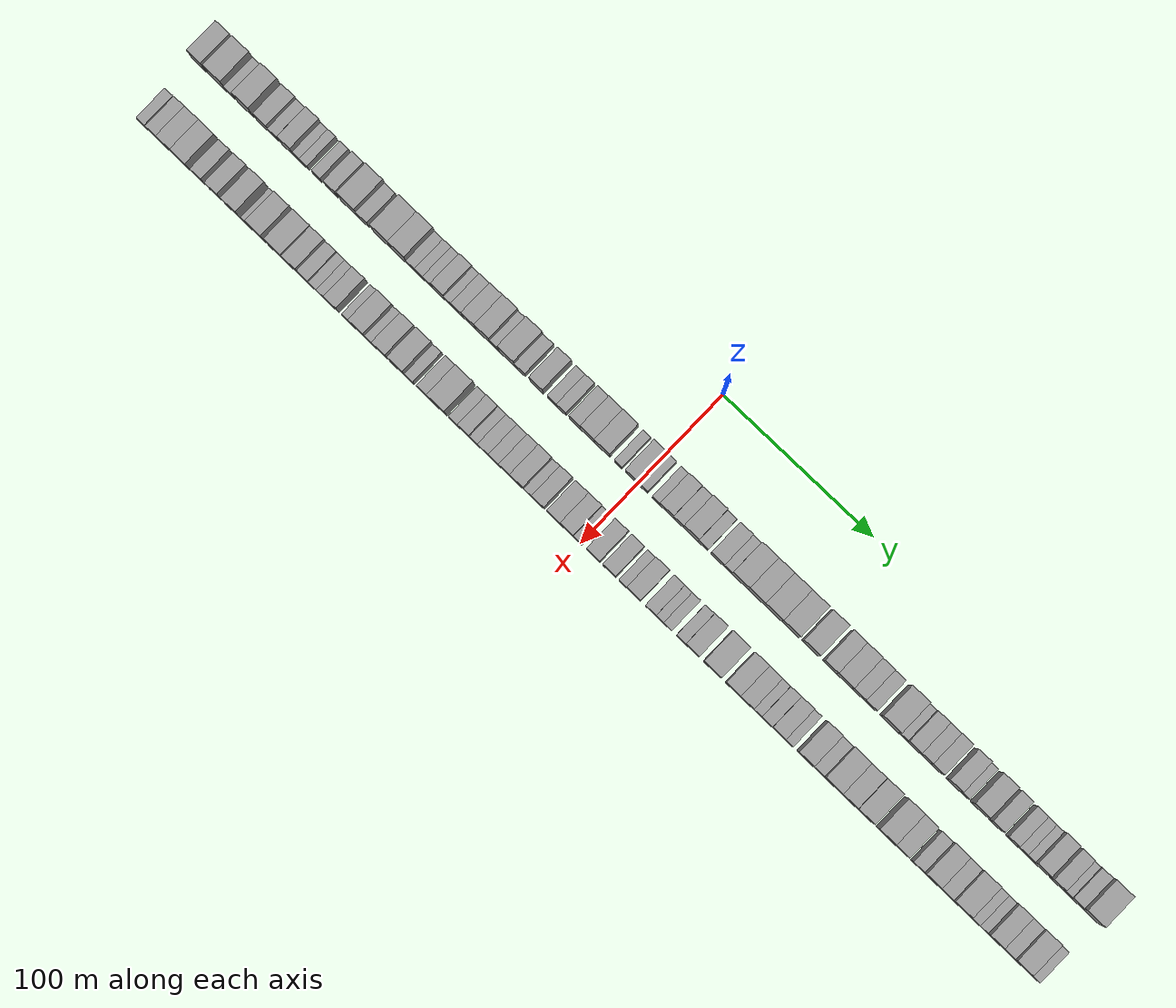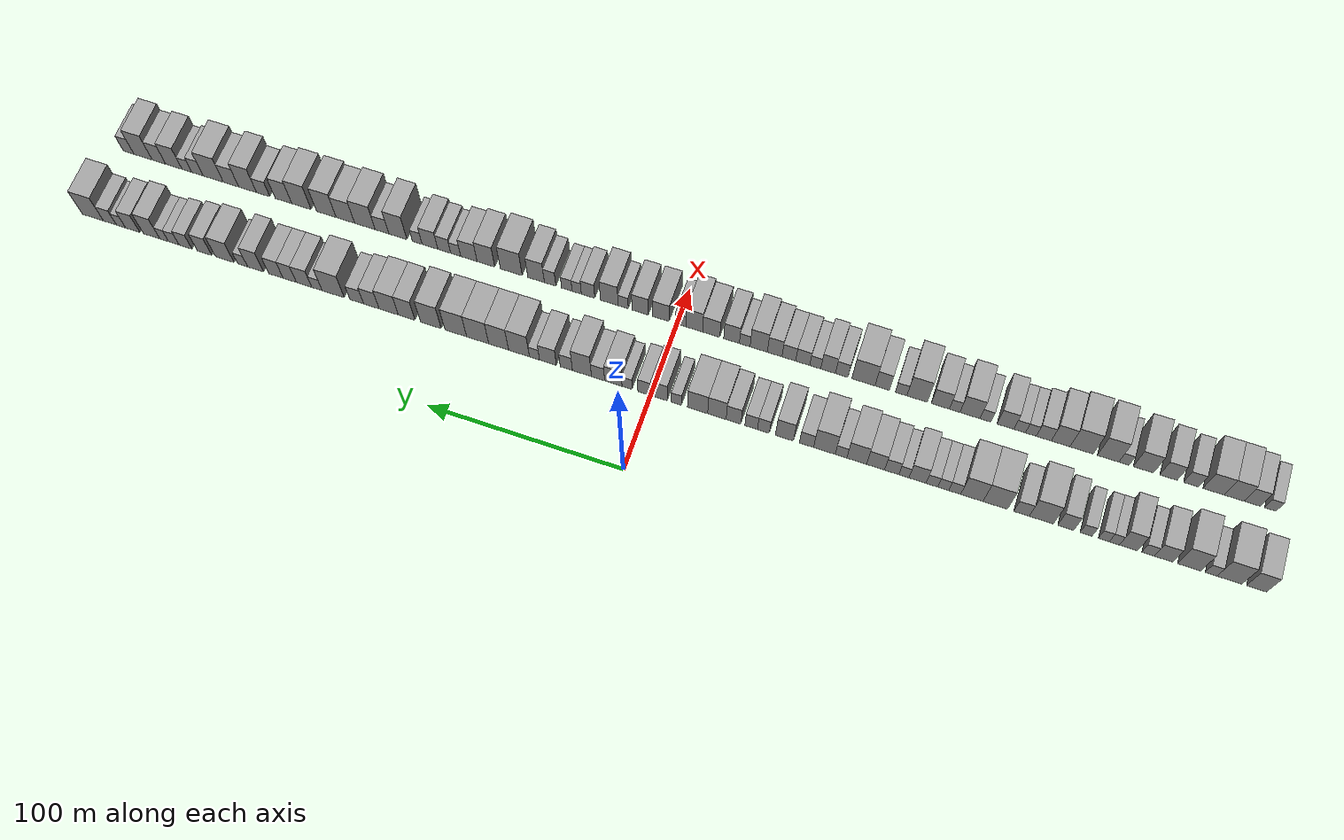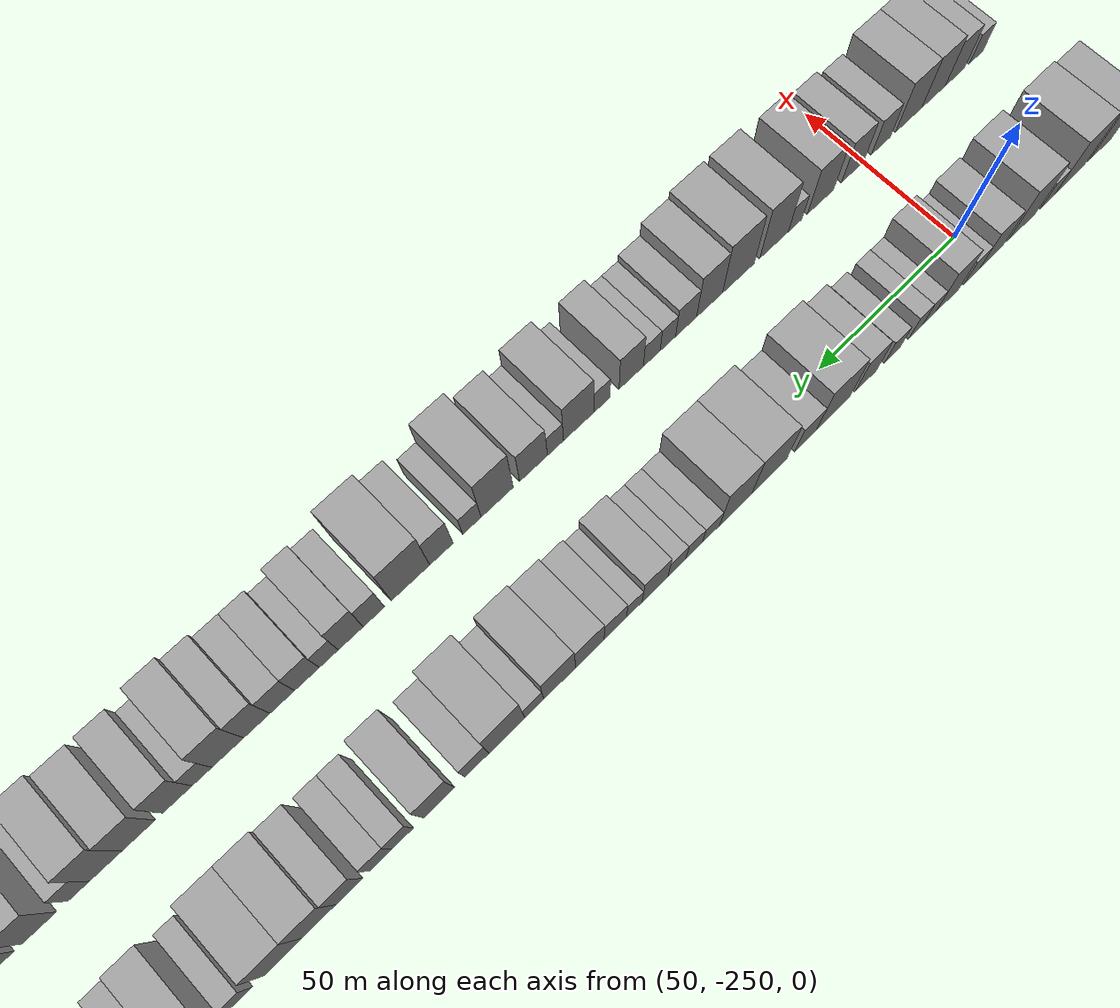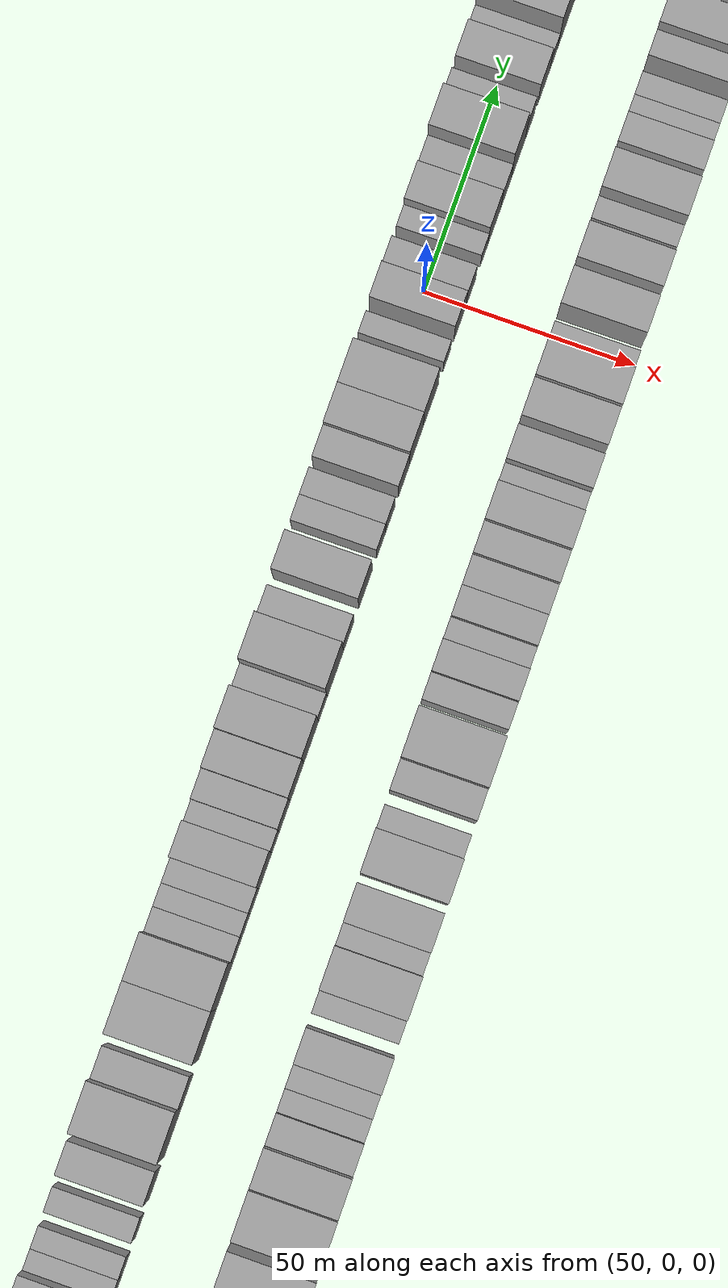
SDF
<sdf version="1.6">
 <world name="default">
  <scene>
   <sky><clouds><speed>12</speed></clouds></sky>
   <ambient>0.4 0.4 0.4 1</ambient>
   <background>0.7 0.7 0.7 1</background>
   <shadows>1</shadows>
  </scene>
  <gravity>0 0 -9.8066</gravity>
  <magnetic_field>6e-06 2.3e-05 -4.2e-05</magnetic_field>
  <physics default="0" name="default_physics" type="ode">
   <ode>
    <solver>
     <type>quick</type>
     <iters>10</iters>
     <sor>1.0</sor>
     <use_dynamic_moi_rescaling>0</use_dynamic_moi_rescaling>
    </solver>
    <constraints>
     <cfm>0</cfm>
     <erp>0.2</erp>
     <contact_max_correcting_vel>100</contact_max_correcting_vel>
     <contact_surface_layer>0.001</contact_surface_layer>
    </constraints>
   </ode>
   <max_step_size>0.004</max_step_size>
   <real_time_factor>1</real_time_factor>
   <real_time_update_rate>250</real_time_update_rate>
  </physics>
  <light name="sun" type="directional">
   <pose>0 0 10 0 0 0</pose>
   <diffuse>0.8 0.8 0.8 1</diffuse>
   <specular>0.2 0.2 0.2 1</specular>
   <attenuation>
    <range>1000</range>
    <constant>0.9</constant>
    <linear>0.01</linear>
    <quadratic>0.001</quadratic>
   </attenuation>
   <direction>-0.5 0.1 -0.9</direction>
  </light>
  <model name="building_1">
   <static>1</static>
   <pose>50.0000 -295.3175 0 0.000000 0.000000 0.000000</pose>
   <link name="link">
    <pose>0 0 10.50 0 0 0</pose>
    <collision name="collision"><geometry><box><size>20.0000 9.3650 21.0000</size></box></geometry></collision>
    <visual name="visual">
     <cast_shadows>0</cast_shadows>
     <geometry><box><size>20.0000 9.3650 21.0000</size></box></geometry>
     <material>
      <script>
       <uri>model://grey_wall/materials/scripts</uri>
       <uri>model://grey_wall/materials/textures</uri>
       <name>vrc/grey_wall</name>
      </script>
     </material>
    </visual>
   </link>
  </model>
  <model name="building_2">
   <static>1</static>
   <pose>50.0000 -282.8107 0 0.000000 0.000000 0.000000</pose>
   <link name="link">
    <pose>0 0 12.00 0 0 0</pose>
    <collision name="collision"><geometry><box><size>20.0000 11.6486 24.0000</size></box></geometry></collision>
    <visual name="visual">
     <cast_shadows>0</cast_shadows>
     <geometry><box><size>20.0000 11.6486 24.0000</size></box></geometry>
     <material>
      <script>
       <uri>model://grey_wall/materials/scripts</uri>
       <uri>model://grey_wall/materials/textures</uri>
       <name>vrc/grey_wall</name>
      </script>
     </material>
    </visual>
   </link>
  </model>
  <model name="building_3">
   <static>1</static>
   <pose>50.0000 -274.1890 0 0.000000 0.000000 0.000000</pose>
   <link name="link">
    <pose>0 0 6.00 0 0 0</pose>
    <collision name="collision"><geometry><box><size>20.0000 5.5949 12.0000</size></box></geometry></collision>
    <visual name="visual">
     <cast_shadows>0</cast_shadows>
     <geometry><box><size>20.0000 5.5949 12.0000</size></box></geometry>
     <material>
      <script>
       <uri>model://grey_wall/materials/scripts</uri>
       <uri>model://grey_wall/materials/textures</uri>
       <name>vrc/grey_wall</name>
      </script>
     </material>
    </visual>
   </link>
  </model>
  <model name="building_4">
   <static>1</static>
   <pose>50.0000 -263.8913 0 0.000000 0.000000 0.000000</pose>
   <link name="link">
    <pose>0 0 12.00 0 0 0</pose>
    <collision name="collision"><geometry><box><size>20.0000 11.0005 24.0000</size></box></geometry></collision>
    <visual name="visual">
     <cast_shadows>0</cast_shadows>
     <geometry><box><size>20.0000 11.0005 24.0000</size></box></geometry>
     <material>
      <script>
       <uri>model://grey_wall/materials/scripts</uri>
       <uri>model://grey_wall/materials/textures</uri>
       <name>vrc/grey_wall</name>
      </script>
     </material>
    </visual>
   </link>
  </model>
  <model name="building_5">
   <static>1</static>
   <pose>50.0000 -251.9345 0 0.000000 0.000000 0.000000</pose>
   <link name="link">
    <pose>0 0 9.00 0 0 0</pose>
    <collision name="collision"><geometry><box><size>20.0000 8.9130 18.0000</size></box></geometry></collision>
    <visual name="visual">
     <cast_shadows>0</cast_shadows>
     <geometry><box><size>20.0000 8.9130 18.0000</size></box></geometry>
     <material>
      <script>
       <uri>model://grey_wall/materials/scripts</uri>
       <uri>model://grey_wall/materials/textures</uri>
       <name>vrc/grey_wall</name>
      </script>
     </material>
    </visual>
   </link>
  </model>
  <model name="building_6">
   <static>1</static>
   <pose>50.0000 -244.5130 0 0.000000 0.000000 0.000000</pose>
   <link name="link">
    <pose>0 0 6.00 0 0 0</pose>
    <collision name="collision"><geometry><box><size>20.0000 5.9301 12.0000</size></box></geometry></collision>
    <visual name="visual">
     <cast_shadows>0</cast_shadows>
     <geometry><box><size>20.0000 5.9301 12.0000</size></box></geometry>
     <material>
      <script>
       <uri>model://grey_wall/materials/scripts</uri>
       <uri>model://grey_wall/materials/textures</uri>
       <name>vrc/grey_wall</name>
      </script>
     </material>
    </visual>
   </link>
  </model>
  <model name="building_7">
   <static>1</static>
   <pose>50.0000 -235.2398 0 0.000000 0.000000 0.000000</pose>
   <link name="link">
    <pose>0 0 10.50 0 0 0</pose>
    <collision name="collision"><geometry><box><size>20.0000 8.6164 21.0000</size></box></geometry></collision>
    <visual name="visual">
     <cast_shadows>0</cast_shadows>
     <geometry><box><size>20.0000 8.6164 21.0000</size></box></geometry>
     <material>
      <script>
       <uri>model://grey_wall/materials/scripts</uri>
       <uri>model://grey_wall/materials/textures</uri>
       <name>vrc/grey_wall</name>
      </script>
     </material>
    </visual>
   </link>
  </model>
  <model name="building_8">
   <static>1</static>
   <pose>50.0000 -228.5288 0 0.000000 0.000000 0.000000</pose>
   <link name="link">
    <pose>0 0 6.00 0 0 0</pose>
    <collision name="collision"><geometry><box><size>20.0000 4.8055 12.0000</size></box></geometry></collision>
    <visual name="visual">
     <cast_shadows>0</cast_shadows>
     <geometry><box><size>20.0000 4.8055 12.0000</size></box></geometry>
     <material>
      <script>
       <uri>model://grey_wall/materials/scripts</uri>
       <uri>model://grey_wall/materials/textures</uri>
       <name>vrc/grey_wall</name>
      </script>
     </material>
    </visual>
   </link>
  </model>
  <model name="building_9">
   <static>1</static>
   <pose>50.0000 -223.5332 0 0.000000 0.000000 0.000000</pose>
   <link name="link">
    <pose>0 0 6.00 0 0 0</pose>
    <collision name="collision"><geometry><box><size>20.0000 5.1856 12.0000</size></box></geometry></collision>
    <visual name="visual">
     <cast_shadows>0</cast_shadows>
     <geometry><box><size>20.0000 5.1856 12.0000</size></box></geometry>
     <material>
      <script>
       <uri>model://grey_wall/materials/scripts</uri>
       <uri>model://grey_wall/materials/textures</uri>
       <name>vrc/grey_wall</name>
      </script>
     </material>
    </visual>
   </link>
  </model>
  <model name="building_10">
   <static>1</static>
   <pose>50.0000 -215.0682 0 0.000000 0.000000 0.000000</pose>
   <link name="link">
    <pose>0 0 6.00 0 0 0</pose>
    <collision name="collision"><geometry><box><size>20.0000 5.7443 12.0000</size></box></geometry></collision>
    <visual name="visual">
     <cast_shadows>0</cast_shadows>
     <geometry><box><size>20.0000 5.7443 12.0000</size></box></geometry>
     <material>
      <script>
       <uri>model://grey_wall/materials/scripts</uri>
       <uri>model://grey_wall/materials/textures</uri>
       <name>vrc/grey_wall</name>
      </script>
     </material>
    </visual>
   </link>
  </model>
  <model name="building_11">
   <static>1</static>
   <pose>50.0000 -205.3281 0 0.000000 0.000000 0.000000</pose>
   <link name="link">
    <pose>0 0 9.00 0 0 0</pose>
    <collision name="collision"><geometry><box><size>20.0000 7.7359 18.0000</size></box></geometry></collision>
    <visual name="visual">
     <cast_shadows>0</cast_shadows>
     <geometry><box><size>20.0000 7.7359 18.0000</size></box></geometry>
     <material>
      <script>
       <uri>model://grey_wall/materials/scripts</uri>
       <uri>model://grey_wall/materials/textures</uri>
       <name>vrc/grey_wall</name>
      </script>
     </material>
    </visual>
   </link>
  </model>
  <model name="building_12">
   <static>1</static>
   <pose>50.0000 -193.6278 0 0.000000 0.000000 0.000000</pose>
   <link name="link">
    <pose>0 0 12.00 0 0 0</pose>
    <collision name="collision"><geometry><box><size>20.0000 11.6648 24.0000</size></box></geometry></collision>
    <visual name="visual">
     <cast_shadows>0</cast_shadows>
     <geometry><box><size>20.0000 11.6648 24.0000</size></box></geometry>
     <material>
      <script>
       <uri>model://grey_wall/materials/scripts</uri>
       <uri>model://grey_wall/materials/textures</uri>
       <name>vrc/grey_wall</name>
      </script>
     </material>
    </visual>
   </link>
  </model>
  <model name="building_13">
   <static>1</static>
   <pose>50.0000 -184.0830 0 0.000000 0.000000 0.000000</pose>
   <link name="link">
    <pose>0 0 7.50 0 0 0</pose>
    <collision name="collision"><geometry><box><size>20.0000 7.4248 15.0000</size></box></geometry></collision>
    <visual name="visual">
     <cast_shadows>0</cast_shadows>
     <geometry><box><size>20.0000 7.4248 15.0000</size></box></geometry>
     <material>
      <script>
       <uri>model://grey_wall/materials/scripts</uri>
       <uri>model://grey_wall/materials/textures</uri>
       <name>vrc/grey_wall</name>
      </script>
     </material>
    </visual>
   </link>
  </model>
  <model name="building_14">
   <static>1</static>
   <pose>50.0000 -171.4516 0 0.000000 0.000000 0.000000</pose>
   <link name="link">
    <pose>0 0 12.00 0 0 0</pose>
    <collision name="collision"><geometry><box><size>20.0000 11.8380 24.0000</size></box></geometry></collision>
    <visual name="visual">
     <cast_shadows>0</cast_shadows>
     <geometry><box><size>20.0000 11.8380 24.0000</size></box></geometry>
     <material>
      <script>
       <uri>model://grey_wall/materials/scripts</uri>
       <uri>model://grey_wall/materials/textures</uri>
       <name>vrc/grey_wall</name>
      </script>
     </material>
    </visual>
   </link>
  </model>
  <model name="building_15">
   <static>1</static>
   <pose>50.0000 -160.0924 0 0.000000 0.000000 0.000000</pose>
   <link name="link">
    <pose>0 0 12.00 0 0 0</pose>
    <collision name="collision"><geometry><box><size>20.0000 10.8804 24.0000</size></box></geometry></collision>
    <visual name="visual">
     <cast_shadows>0</cast_shadows>
     <geometry><box><size>20.0000 10.8804 24.0000</size></box></geometry>
     <material>
      <script>
       <uri>model://grey_wall/materials/scripts</uri>
       <uri>model://grey_wall/materials/textures</uri>
       <name>vrc/grey_wall</name>
      </script>
     </material>
    </visual>
   </link>
  </model>
  <model name="building_16">
   <static>1</static>
   <pose>50.0000 -151.7578 0 0.000000 0.000000 0.000000</pose>
   <link name="link">
    <pose>0 0 6.00 0 0 0</pose>
    <collision name="collision"><geometry><box><size>20.0000 5.7887 12.0000</size></box></geometry></collision>
    <visual name="visual">
     <cast_shadows>0</cast_shadows>
     <geometry><box><size>20.0000 5.7887 12.0000</size></box></geometry>
     <material>
      <script>
       <uri>model://grey_wall/materials/scripts</uri>
       <uri>model://grey_wall/materials/textures</uri>
       <name>vrc/grey_wall</name>
      </script>
     </material>
    </visual>
   </link>
  </model>
  <model name="building_17">
   <static>1</static>
   <pose>50.0000 -146.1758 0 0.000000 0.000000 0.000000</pose>
   <link name="link">
    <pose>0 0 6.00 0 0 0</pose>
    <collision name="collision"><geometry><box><size>20.0000 5.3753 12.0000</size></box></geometry></collision>
    <visual name="visual">
     <cast_shadows>0</cast_shadows>
     <geometry><box><size>20.0000 5.3753 12.0000</size></box></geometry>
     <material>
      <script>
       <uri>model://grey_wall/materials/scripts</uri>
       <uri>model://grey_wall/materials/textures</uri>
       <name>vrc/grey_wall</name>
      </script>
     </material>
    </visual>
   </link>
  </model>
  <model name="building_18">
   <static>1</static>
   <pose>50.0000 -140.6003 0 0.000000 0.000000 0.000000</pose>
   <link name="link">
    <pose>0 0 6.00 0 0 0</pose>
    <collision name="collision"><geometry><box><size>20.0000 5.7758 12.0000</size></box></geometry></collision>
    <visual name="visual">
     <cast_shadows>0</cast_shadows>
     <geometry><box><size>20.0000 5.7758 12.0000</size></box></geometry>
     <material>
      <script>
       <uri>model://grey_wall/materials/scripts</uri>
       <uri>model://grey_wall/materials/textures</uri>
       <name>vrc/grey_wall</name>
      </script>
     </material>
    </visual>
   </link>
  </model>
  <model name="building_19">
   <static>1</static>
   <pose>50.0000 -133.5268 0 0.000000 0.000000 0.000000</pose>
   <link name="link">
    <pose>0 0 9.00 0 0 0</pose>
    <collision name="collision"><geometry><box><size>20.0000 8.3712 18.0000</size></box></geometry></collision>
    <visual name="visual">
     <cast_shadows>0</cast_shadows>
     <geometry><box><size>20.0000 8.3712 18.0000</size></box></geometry>
     <material>
      <script>
       <uri>model://grey_wall/materials/scripts</uri>
       <uri>model://grey_wall/materials/textures</uri>
       <name>vrc/grey_wall</name>
      </script>
     </material>
    </visual>
   </link>
  </model>
  <model name="building_20">
   <static>1</static>
   <pose>50.0000 -126.8570 0 0.000000 0.000000 0.000000</pose>
   <link name="link">
    <pose>0 0 6.00 0 0 0</pose>
    <collision name="collision"><geometry><box><size>20.0000 4.9683 12.0000</size></box></geometry></collision>
    <visual name="visual">
     <cast_shadows>0</cast_shadows>
     <geometry><box><size>20.0000 4.9683 12.0000</size></box></geometry>
     <material>
      <script>
       <uri>model://grey_wall/materials/scripts</uri>
       <uri>model://grey_wall/materials/textures</uri>
       <name>vrc/grey_wall</name>
      </script>
     </material>
    </visual>
   </link>
  </model>
  <model name="building_21">
   <static>1</static>
   <pose>50.0000 -120.8502 0 0.000000 0.000000 0.000000</pose>
   <link name="link">
    <pose>0 0 7.50 0 0 0</pose>
    <collision name="collision"><geometry><box><size>20.0000 7.0453 15.0000</size></box></geometry></collision>
    <visual name="visual">
     <cast_shadows>0</cast_shadows>
     <geometry><box><size>20.0000 7.0453 15.0000</size></box></geometry>
     <material>
      <script>
       <uri>model://grey_wall/materials/scripts</uri>
       <uri>model://grey_wall/materials/textures</uri>
       <name>vrc/grey_wall</name>
      </script>
     </material>
    </visual>
   </link>
  </model>
  <model name="building_22">
   <static>1</static>
   <pose>50.0000 -112.8907 0 0.000000 0.000000 0.000000</pose>
   <link name="link">
    <pose>0 0 9.00 0 0 0</pose>
    <collision name="collision"><geometry><box><size>20.0000 8.8738 18.0000</size></box></geometry></collision>
    <visual name="visual">
     <cast_shadows>0</cast_shadows>
     <geometry><box><size>20.0000 8.8738 18.0000</size></box></geometry>
     <material>
      <script>
       <uri>model://grey_wall/materials/scripts</uri>
       <uri>model://grey_wall/materials/textures</uri>
       <name>vrc/grey_wall</name>
      </script>
     </material>
    </visual>
   </link>
  </model>
  <model name="building_23">
   <static>1</static>
   <pose>50.0000 -103.5695 0 0.000000 0.000000 0.000000</pose>
   <link name="link">
    <pose>0 0 10.50 0 0 0</pose>
    <collision name="collision"><geometry><box><size>20.0000 9.7686 21.0000</size></box></geometry></collision>
    <visual name="visual">
     <cast_shadows>0</cast_shadows>
     <geometry><box><size>20.0000 9.7686 21.0000</size></box></geometry>
     <material>
      <script>
       <uri>model://grey_wall/materials/scripts</uri>
       <uri>model://grey_wall/materials/textures</uri>
       <name>vrc/grey_wall</name>
      </script>
     </material>
    </visual>
   </link>
  </model>
  <model name="building_24">
   <static>1</static>
   <pose>50.0000 -95.7986 0 0.000000 0.000000 0.000000</pose>
   <link name="link">
    <pose>0 0 6.00 0 0 0</pose>
    <collision name="collision"><geometry><box><size>20.0000 5.7732 12.0000</size></box></geometry></collision>
    <visual name="visual">
     <cast_shadows>0</cast_shadows>
     <geometry><box><size>20.0000 5.7732 12.0000</size></box></geometry>
     <material>
      <script>
       <uri>model://grey_wall/materials/scripts</uri>
       <uri>model://grey_wall/materials/textures</uri>
       <name>vrc/grey_wall</name>
      </script>
     </material>
    </visual>
   </link>
  </model>
  <model name="building_25">
   <static>1</static>
   <pose>50.0000 -87.5383 0 0.000000 0.000000 0.000000</pose>
   <link name="link">
    <pose>0 0 12.00 0 0 0</pose>
    <collision name="collision"><geometry><box><size>20.0000 10.7474 24.0000</size></box></geometry></collision>
    <visual name="visual">
     <cast_shadows>0</cast_shadows>
     <geometry><box><size>20.0000 10.7474 24.0000</size></box></geometry>
     <material>
      <script>
       <uri>model://grey_wall/materials/scripts</uri>
       <uri>model://grey_wall/materials/textures</uri>
       <name>vrc/grey_wall</name>
      </script>
     </material>
    </visual>
   </link>
  </model>
  <model name="building_26">
   <static>1</static>
   <pose>50.0000 -78.6126 0 0.000000 0.000000 0.000000</pose>
   <link name="link">
    <pose>0 0 7.50 0 0 0</pose>
    <collision name="collision"><geometry><box><size>20.0000 7.1039 15.0000</size></box></geometry></collision>
    <visual name="visual">
     <cast_shadows>0</cast_shadows>
     <geometry><box><size>20.0000 7.1039 15.0000</size></box></geometry>
     <material>
      <script>
       <uri>model://grey_wall/materials/scripts</uri>
       <uri>model://grey_wall/materials/textures</uri>
       <name>vrc/grey_wall</name>
      </script>
     </material>
    </visual>
   </link>
  </model>
  <model name="building_27">
   <static>1</static>
   <pose>50.0000 -67.5679 0 0.000000 0.000000 0.000000</pose>
   <link name="link">
    <pose>0 0 10.50 0 0 0</pose>
    <collision name="collision"><geometry><box><size>20.0000 8.9856 21.0000</size></box></geometry></collision>
    <visual name="visual">
     <cast_shadows>0</cast_shadows>
     <geometry><box><size>20.0000 8.9856 21.0000</size></box></geometry>
     <material>
      <script>
       <uri>model://grey_wall/materials/scripts</uri>
       <uri>model://grey_wall/materials/textures</uri>
       <name>vrc/grey_wall</name>
      </script>
     </material>
    </visual>
   </link>
  </model>
  <model name="building_28">
   <static>1</static>
   <pose>50.0000 -57.0685 0 0.000000 0.000000 0.000000</pose>
   <link name="link">
    <pose>0 0 7.50 0 0 0</pose>
    <collision name="collision"><geometry><box><size>20.0000 6.0131 15.0000</size></box></geometry></collision>
    <visual name="visual">
     <cast_shadows>0</cast_shadows>
     <geometry><box><size>20.0000 6.0131 15.0000</size></box></geometry>
     <material>
      <script>
       <uri>model://grey_wall/materials/scripts</uri>
       <uri>model://grey_wall/materials/textures</uri>
       <name>vrc/grey_wall</name>
      </script>
     </material>
    </visual>
   </link>
  </model>
  <model name="building_29">
   <static>1</static>
   <pose>50.0000 -50.8885 0 0.000000 0.000000 0.000000</pose>
   <link name="link">
    <pose>0 0 7.50 0 0 0</pose>
    <collision name="collision"><geometry><box><size>20.0000 6.3470 15.0000</size></box></geometry></collision>
    <visual name="visual">
     <cast_shadows>0</cast_shadows>
     <geometry><box><size>20.0000 6.3470 15.0000</size></box></geometry>
     <material>
      <script>
       <uri>model://grey_wall/materials/scripts</uri>
       <uri>model://grey_wall/materials/textures</uri>
       <name>vrc/grey_wall</name>
      </script>
     </material>
    </visual>
   </link>
  </model>
  <model name="building_30">
   <static>1</static>
   <pose>50.0000 -41.9861 0 0.000000 0.000000 0.000000</pose>
   <link name="link">
    <pose>0 0 9.00 0 0 0</pose>
    <collision name="collision"><geometry><box><size>20.0000 7.4578 18.0000</size></box></geometry></collision>
    <visual name="visual">
     <cast_shadows>0</cast_shadows>
     <geometry><box><size>20.0000 7.4578 18.0000</size></box></geometry>
     <material>
      <script>
       <uri>model://grey_wall/materials/scripts</uri>
       <uri>model://grey_wall/materials/textures</uri>
       <name>vrc/grey_wall</name>
      </script>
     </material>
    </visual>
   </link>
  </model>
  <model name="building_31">
   <static>1</static>
   <pose>50.0000 -33.5933 0 0.000000 0.000000 0.000000</pose>
   <link name="link">
    <pose>0 0 10.50 0 0 0</pose>
    <collision name="collision"><geometry><box><size>20.0000 9.3279 21.0000</size></box></geometry></collision>
    <visual name="visual">
     <cast_shadows>0</cast_shadows>
     <geometry><box><size>20.0000 9.3279 21.0000</size></box></geometry>
     <material>
      <script>
       <uri>model://grey_wall/materials/scripts</uri>
       <uri>model://grey_wall/materials/textures</uri>
       <name>vrc/grey_wall</name>
      </script>
     </material>
    </visual>
   </link>
  </model>
  <model name="building_32">
   <static>1</static>
   <pose>50.0000 -23.7865 0 0.000000 0.000000 0.000000</pose>
   <link name="link">
    <pose>0 0 10.50 0 0 0</pose>
    <collision name="collision"><geometry><box><size>20.0000 10.2857 21.0000</size></box></geometry></collision>
    <visual name="visual">
     <cast_shadows>0</cast_shadows>
     <geometry><box><size>20.0000 10.2857 21.0000</size></box></geometry>
     <material>
      <script>
       <uri>model://grey_wall/materials/scripts</uri>
       <uri>model://grey_wall/materials/textures</uri>
       <name>vrc/grey_wall</name>
      </script>
     </material>
    </visual>
   </link>
  </model>
  <model name="building_33">
   <static>1</static>
   <pose>50.0000 -13.0210 0 0.000000 0.000000 0.000000</pose>
   <link name="link">
    <pose>0 0 6.00 0 0 0</pose>
    <collision name="collision"><geometry><box><size>20.0000 5.2452 12.0000</size></box></geometry></collision>
    <visual name="visual">
     <cast_shadows>0</cast_shadows>
     <geometry><box><size>20.0000 5.2452 12.0000</size></box></geometry>
     <material>
      <script>
       <uri>model://grey_wall/materials/scripts</uri>
       <uri>model://grey_wall/materials/textures</uri>
       <name>vrc/grey_wall</name>
      </script>
     </material>
    </visual>
   </link>
  </model>
  <model name="building_34">
   <static>1</static>
   <pose>50.0000 -4.1912 0 0.000000 0.000000 0.000000</pose>
   <link name="link">
    <pose>0 0 9.00 0 0 0</pose>
    <collision name="collision"><geometry><box><size>20.0000 8.4145 18.0000</size></box></geometry></collision>
    <visual name="visual">
     <cast_shadows>0</cast_shadows>
     <geometry><box><size>20.0000 8.4145 18.0000</size></box></geometry>
     <material>
      <script>
       <uri>model://grey_wall/materials/scripts</uri>
       <uri>model://grey_wall/materials/textures</uri>
       <name>vrc/grey_wall</name>
      </script>
     </material>
    </visual>
   </link>
  </model>
  <model name="building_35">
   <static>1</static>
   <pose>50.0000 3.3389 0 0.000000 0.000000 0.000000</pose>
   <link name="link">
    <pose>0 0 7.50 0 0 0</pose>
    <collision name="collision"><geometry><box><size>20.0000 6.6458 15.0000</size></box></geometry></collision>
    <visual name="visual">
     <cast_shadows>0</cast_shadows>
     <geometry><box><size>20.0000 6.6458 15.0000</size></box></geometry>
     <material>
      <script>
       <uri>model://grey_wall/materials/scripts</uri>
       <uri>model://grey_wall/materials/textures</uri>
       <name>vrc/grey_wall</name>
      </script>
     </material>
    </visual>
   </link>
  </model>
  <model name="building_36">
   <static>1</static>
   <pose>50.0000 12.2295 0 0.000000 0.000000 0.000000</pose>
   <link name="link">
    <pose>0 0 6.00 0 0 0</pose>
    <collision name="collision"><geometry><box><size>20.0000 5.1353 12.0000</size></box></geometry></collision>
    <visual name="visual">
     <cast_shadows>0</cast_shadows>
     <geometry><box><size>20.0000 5.1353 12.0000</size></box></geometry>
     <material>
      <script>
       <uri>model://grey_wall/materials/scripts</uri>
       <uri>model://grey_wall/materials/textures</uri>
       <name>vrc/grey_wall</name>
      </script>
     </material>
    </visual>
   </link>
  </model>
  <model name="building_37">
   <static>1</static>
   <pose>50.0000 19.2701 0 0.000000 0.000000 0.000000</pose>
   <link name="link">
    <pose>0 0 9.00 0 0 0</pose>
    <collision name="collision"><geometry><box><size>20.0000 8.9459 18.0000</size></box></geometry></collision>
    <visual name="visual">
     <cast_shadows>0</cast_shadows>
     <geometry><box><size>20.0000 8.9459 18.0000</size></box></geometry>
     <material>
      <script>
       <uri>model://grey_wall/materials/scripts</uri>
       <uri>model://grey_wall/materials/textures</uri>
       <name>vrc/grey_wall</name>
      </script>
     </material>
    </visual>
   </link>
  </model>
  <model name="building_38">
   <static>1</static>
   <pose>50.0000 27.1577 0 0.000000 0.000000 0.000000</pose>
   <link name="link">
    <pose>0 0 7.50 0 0 0</pose>
    <collision name="collision"><geometry><box><size>20.0000 6.8295 15.0000</size></box></geometry></collision>
    <visual name="visual">
     <cast_shadows>0</cast_shadows>
     <geometry><box><size>20.0000 6.8295 15.0000</size></box></geometry>
     <material>
      <script>
       <uri>model://grey_wall/materials/scripts</uri>
       <uri>model://grey_wall/materials/textures</uri>
       <name>vrc/grey_wall</name>
      </script>
     </material>
    </visual>
   </link>
  </model>
  <model name="building_39">
   <static>1</static>
   <pose>50.0000 35.4678 0 0.000000 0.000000 0.000000</pose>
   <link name="link">
    <pose>0 0 12.00 0 0 0</pose>
    <collision name="collision"><geometry><box><size>20.0000 9.7906 24.0000</size></box></geometry></collision>
    <visual name="visual">
     <cast_shadows>0</cast_shadows>
     <geometry><box><size>20.0000 9.7906 24.0000</size></box></geometry>
     <material>
      <script>
       <uri>model://grey_wall/materials/scripts</uri>
       <uri>model://grey_wall/materials/textures</uri>
       <name>vrc/grey_wall</name>
      </script>
     </material>
    </visual>
   </link>
  </model>
  <model name="building_40">
   <static>1</static>
   <pose>50.0000 43.5273 0 0.000000 0.000000 0.000000</pose>
   <link name="link">
    <pose>0 0 7.50 0 0 0</pose>
    <collision name="collision"><geometry><box><size>20.0000 6.3284 15.0000</size></box></geometry></collision>
    <visual name="visual">
     <cast_shadows>0</cast_shadows>
     <geometry><box><size>20.0000 6.3284 15.0000</size></box></geometry>
     <material>
      <script>
       <uri>model://grey_wall/materials/scripts</uri>
       <uri>model://grey_wall/materials/textures</uri>
       <name>vrc/grey_wall</name>
      </script>
     </material>
    </visual>
   </link>
  </model>
  <model name="building_41">
   <static>1</static>
   <pose>50.0000 53.0629 0 0.000000 0.000000 0.000000</pose>
   <link name="link">
    <pose>0 0 9.00 0 0 0</pose>
    <collision name="collision"><geometry><box><size>20.0000 8.7427 18.0000</size></box></geometry></collision>
    <visual name="visual">
     <cast_shadows>0</cast_shadows>
     <geometry><box><size>20.0000 8.7427 18.0000</size></box></geometry>
     <material>
      <script>
       <uri>model://grey_wall/materials/scripts</uri>
       <uri>model://grey_wall/materials/textures</uri>
       <name>vrc/grey_wall</name>
      </script>
     </material>
    </visual>
   </link>
  </model>
  <model name="building_42">
   <static>1</static>
   <pose>50.0000 60.0749 0 0.000000 0.000000 0.000000</pose>
   <link name="link">
    <pose>0 0 6.00 0 0 0</pose>
    <collision name="collision"><geometry><box><size>20.0000 5.2812 12.0000</size></box></geometry></collision>
    <visual name="visual">
     <cast_shadows>0</cast_shadows>
     <geometry><box><size>20.0000 5.2812 12.0000</size></box></geometry>
     <material>
      <script>
       <uri>model://grey_wall/materials/scripts</uri>
       <uri>model://grey_wall/materials/textures</uri>
       <name>vrc/grey_wall</name>
      </script>
     </material>
    </visual>
   </link>
  </model>
  <model name="building_43">
   <static>1</static>
   <pose>50.0000 68.1646 0 0.000000 0.000000 0.000000</pose>
   <link name="link">
    <pose>0 0 12.00 0 0 0</pose>
    <collision name="collision"><geometry><box><size>20.0000 10.8982 24.0000</size></box></geometry></collision>
    <visual name="visual">
     <cast_shadows>0</cast_shadows>
     <geometry><box><size>20.0000 10.8982 24.0000</size></box></geometry>
     <material>
      <script>
       <uri>model://grey_wall/materials/scripts</uri>
       <uri>model://grey_wall/materials/textures</uri>
       <name>vrc/grey_wall</name>
      </script>
     </material>
    </visual>
   </link>
  </model>
  <model name="building_44">
   <static>1</static>
   <pose>50.0000 78.8283 0 0.000000 0.000000 0.000000</pose>
   <link name="link">
    <pose>0 0 12.00 0 0 0</pose>
    <collision name="collision"><geometry><box><size>20.0000 10.4291 24.0000</size></box></geometry></collision>
    <visual name="visual">
     <cast_shadows>0</cast_shadows>
     <geometry><box><size>20.0000 10.4291 24.0000</size></box></geometry>
     <material>
      <script>
       <uri>model://grey_wall/materials/scripts</uri>
       <uri>model://grey_wall/materials/textures</uri>
       <name>vrc/grey_wall</name>
      </script>
     </material>
    </visual>
   </link>
  </model>
  <model name="building_45">
   <static>1</static>
   <pose>50.0000 89.8818 0 0.000000 0.000000 0.000000</pose>
   <link name="link">
    <pose>0 0 12.00 0 0 0</pose>
    <collision name="collision"><geometry><box><size>20.0000 11.6781 24.0000</size></box></geometry></collision>
    <visual name="visual">
     <cast_shadows>0</cast_shadows>
     <geometry><box><size>20.0000 11.6781 24.0000</size></box></geometry>
     <material>
      <script>
       <uri>model://grey_wall/materials/scripts</uri>
       <uri>model://grey_wall/materials/textures</uri>
       <name>vrc/grey_wall</name>
      </script>
     </material>
    </visual>
   </link>
  </model>
  <model name="building_46">
   <static>1</static>
   <pose>50.0000 101.4407 0 0.000000 0.000000 0.000000</pose>
   <link name="link">
    <pose>0 0 12.00 0 0 0</pose>
    <collision name="collision"><geometry><box><size>20.0000 11.4396 24.0000</size></box></geometry></collision>
    <visual name="visual">
     <cast_shadows>0</cast_shadows>
     <geometry><box><size>20.0000 11.4396 24.0000</size></box></geometry>
     <material>
      <script>
       <uri>model://grey_wall/materials/scripts</uri>
       <uri>model://grey_wall/materials/textures</uri>
       <name>vrc/grey_wall</name>
      </script>
     </material>
    </visual>
   </link>
  </model>
  <model name="building_47">
   <static>1</static>
   <pose>50.0000 114.6288 0 0.000000 0.000000 0.000000</pose>
   <link name="link">
    <pose>0 0 12.00 0 0 0</pose>
    <collision name="collision"><geometry><box><size>20.0000 10.9366 24.0000</size></box></geometry></collision>
    <visual name="visual">
     <cast_shadows>0</cast_shadows>
     <geometry><box><size>20.0000 10.9366 24.0000</size></box></geometry>
     <material>
      <script>
       <uri>model://grey_wall/materials/scripts</uri>
       <uri>model://grey_wall/materials/textures</uri>
       <name>vrc/grey_wall</name>
      </script>
     </material>
    </visual>
   </link>
  </model>
  <model name="building_48">
   <static>1</static>
   <pose>50.0000 127.5241 0 0.000000 0.000000 0.000000</pose>
   <link name="link">
    <pose>0 0 10.50 0 0 0</pose>
    <collision name="collision"><geometry><box><size>20.0000 8.8540 21.0000</size></box></geometry></collision>
    <visual name="visual">
     <cast_shadows>0</cast_shadows>
     <geometry><box><size>20.0000 8.8540 21.0000</size></box></geometry>
     <material>
      <script>
       <uri>model://grey_wall/materials/scripts</uri>
       <uri>model://grey_wall/materials/textures</uri>
       <name>vrc/grey_wall</name>
      </script>
     </material>
    </visual>
   </link>
  </model>
  <model name="building_49">
   <static>1</static>
   <pose>50.0000 137.0890 0 0.000000 0.000000 0.000000</pose>
   <link name="link">
    <pose>0 0 10.50 0 0 0</pose>
    <collision name="collision"><geometry><box><size>20.0000 10.2759 21.0000</size></box></geometry></collision>
    <visual name="visual">
     <cast_shadows>0</cast_shadows>
     <geometry><box><size>20.0000 10.2759 21.0000</size></box></geometry>
     <material>
      <script>
       <uri>model://grey_wall/materials/scripts</uri>
       <uri>model://grey_wall/materials/textures</uri>
       <name>vrc/grey_wall</name>
      </script>
     </material>
    </visual>
   </link>
  </model>
  <model name="building_50">
   <static>1</static>
   <pose>50.0000 146.3856 0 0.000000 0.000000 0.000000</pose>
   <link name="link">
    <pose>0 0 9.00 0 0 0</pose>
    <collision name="collision"><geometry><box><size>20.0000 8.3173 18.0000</size></box></geometry></collision>
    <visual name="visual">
     <cast_shadows>0</cast_shadows>
     <geometry><box><size>20.0000 8.3173 18.0000</size></box></geometry>
     <material>
      <script>
       <uri>model://grey_wall/materials/scripts</uri>
       <uri>model://grey_wall/materials/textures</uri>
       <name>vrc/grey_wall</name>
      </script>
     </material>
    </visual>
   </link>
  </model>
  <model name="building_51">
   <static>1</static>
   <pose>50.0000 154.2314 0 0.000000 0.000000 0.000000</pose>
   <link name="link">
    <pose>0 0 7.50 0 0 0</pose>
    <collision name="collision"><geometry><box><size>20.0000 7.3743 15.0000</size></box></geometry></collision>
    <visual name="visual">
     <cast_shadows>0</cast_shadows>
     <geometry><box><size>20.0000 7.3743 15.0000</size></box></geometry>
     <material>
      <script>
       <uri>model://grey_wall/materials/scripts</uri>
       <uri>model://grey_wall/materials/textures</uri>
       <name>vrc/grey_wall</name>
      </script>
     </material>
    </visual>
   </link>
  </model>
  <model name="building_52">
   <static>1</static>
   <pose>50.0000 166.8881 0 0.000000 0.000000 0.000000</pose>
   <link name="link">
    <pose>0 0 12.00 0 0 0</pose>
    <collision name="collision"><geometry><box><size>20.0000 11.9390 24.0000</size></box></geometry></collision>
    <visual name="visual">
     <cast_shadows>0</cast_shadows>
     <geometry><box><size>20.0000 11.9390 24.0000</size></box></geometry>
     <material>
      <script>
       <uri>model://grey_wall/materials/scripts</uri>
       <uri>model://grey_wall/materials/textures</uri>
       <name>vrc/grey_wall</name>
      </script>
     </material>
    </visual>
   </link>
  </model>
  <model name="building_53">
   <static>1</static>
   <pose>50.0000 175.6898 0 0.000000 0.000000 0.000000</pose>
   <link name="link">
    <pose>0 0 6.00 0 0 0</pose>
    <collision name="collision"><geometry><box><size>20.0000 5.6643 12.0000</size></box></geometry></collision>
    <visual name="visual">
     <cast_shadows>0</cast_shadows>
     <geometry><box><size>20.0000 5.6643 12.0000</size></box></geometry>
     <material>
      <script>
       <uri>model://grey_wall/materials/scripts</uri>
       <uri>model://grey_wall/materials/textures</uri>
       <name>vrc/grey_wall</name>
      </script>
     </material>
    </visual>
   </link>
  </model>
  <model name="building_54">
   <static>1</static>
   <pose>50.0000 182.6710 0 0.000000 0.000000 0.000000</pose>
   <link name="link">
    <pose>0 0 9.00 0 0 0</pose>
    <collision name="collision"><geometry><box><size>20.0000 8.2981 18.0000</size></box></geometry></collision>
    <visual name="visual">
     <cast_shadows>0</cast_shadows>
     <geometry><box><size>20.0000 8.2981 18.0000</size></box></geometry>
     <material>
      <script>
       <uri>model://grey_wall/materials/scripts</uri>
       <uri>model://grey_wall/materials/textures</uri>
       <name>vrc/grey_wall</name>
      </script>
     </material>
    </visual>
   </link>
  </model>
  <model name="building_55">
   <static>1</static>
   <pose>50.0000 190.4304 0 0.000000 0.000000 0.000000</pose>
   <link name="link">
    <pose>0 0 9.00 0 0 0</pose>
    <collision name="collision"><geometry><box><size>20.0000 7.2208 18.0000</size></box></geometry></collision>
    <visual name="visual">
     <cast_shadows>0</cast_shadows>
     <geometry><box><size>20.0000 7.2208 18.0000</size></box></geometry>
     <material>
      <script>
       <uri>model://grey_wall/materials/scripts</uri>
       <uri>model://grey_wall/materials/textures</uri>
       <name>vrc/grey_wall</name>
      </script>
     </material>
    </visual>
   </link>
  </model>
  <model name="building_56">
   <static>1</static>
   <pose>50.0000 197.8880 0 0.000000 0.000000 0.000000</pose>
   <link name="link">
    <pose>0 0 9.00 0 0 0</pose>
    <collision name="collision"><geometry><box><size>20.0000 7.6944 18.0000</size></box></geometry></collision>
    <visual name="visual">
     <cast_shadows>0</cast_shadows>
     <geometry><box><size>20.0000 7.6944 18.0000</size></box></geometry>
     <material>
      <script>
       <uri>model://grey_wall/materials/scripts</uri>
       <uri>model://grey_wall/materials/textures</uri>
       <name>vrc/grey_wall</name>
      </script>
     </material>
    </visual>
   </link>
  </model>
  <model name="building_57">
   <static>1</static>
   <pose>50.0000 209.0783 0 0.000000 0.000000 0.000000</pose>
   <link name="link">
    <pose>0 0 10.50 0 0 0</pose>
    <collision name="collision"><geometry><box><size>20.0000 8.6862 21.0000</size></box></geometry></collision>
    <visual name="visual">
     <cast_shadows>0</cast_shadows>
     <geometry><box><size>20.0000 8.6862 21.0000</size></box></geometry>
     <material>
      <script>
       <uri>model://grey_wall/materials/scripts</uri>
       <uri>model://grey_wall/materials/textures</uri>
       <name>vrc/grey_wall</name>
      </script>
     </material>
    </visual>
   </link>
  </model>
  <model name="building_58">
   <static>1</static>
   <pose>50.0000 216.1518 0 0.000000 0.000000 0.000000</pose>
   <link name="link">
    <pose>0 0 6.00 0 0 0</pose>
    <collision name="collision"><geometry><box><size>20.0000 5.4607 12.0000</size></box></geometry></collision>
    <visual name="visual">
     <cast_shadows>0</cast_shadows>
     <geometry><box><size>20.0000 5.4607 12.0000</size></box></geometry>
     <material>
      <script>
       <uri>model://grey_wall/materials/scripts</uri>
       <uri>model://grey_wall/materials/textures</uri>
       <name>vrc/grey_wall</name>
      </script>
     </material>
    </visual>
   </link>
  </model>
  <model name="building_59">
   <static>1</static>
   <pose>50.0000 225.9751 0 0.000000 0.000000 0.000000</pose>
   <link name="link">
    <pose>0 0 10.50 0 0 0</pose>
    <collision name="collision"><geometry><box><size>20.0000 10.1858 21.0000</size></box></geometry></collision>
    <visual name="visual">
     <cast_shadows>0</cast_shadows>
     <geometry><box><size>20.0000 10.1858 21.0000</size></box></geometry>
     <material>
      <script>
       <uri>model://grey_wall/materials/scripts</uri>
       <uri>model://grey_wall/materials/textures</uri>
       <name>vrc/grey_wall</name>
      </script>
     </material>
    </visual>
   </link>
  </model>
  <model name="building_60">
   <static>1</static>
   <pose>50.0000 237.0430 0 0.000000 0.000000 0.000000</pose>
   <link name="link">
    <pose>0 0 9.00 0 0 0</pose>
    <collision name="collision"><geometry><box><size>20.0000 7.9501 18.0000</size></box></geometry></collision>
    <visual name="visual">
     <cast_shadows>0</cast_shadows>
     <geometry><box><size>20.0000 7.9501 18.0000</size></box></geometry>
     <material>
      <script>
       <uri>model://grey_wall/materials/scripts</uri>
       <uri>model://grey_wall/materials/textures</uri>
       <name>vrc/grey_wall</name>
      </script>
     </material>
    </visual>
   </link>
  </model>
  <model name="building_61">
   <static>1</static>
   <pose>50.0000 247.5973 0 0.000000 0.000000 0.000000</pose>
   <link name="link">
    <pose>0 0 7.50 0 0 0</pose>
    <collision name="collision"><geometry><box><size>20.0000 7.1584 15.0000</size></box></geometry></collision>
    <visual name="visual">
     <cast_shadows>0</cast_shadows>
     <geometry><box><size>20.0000 7.1584 15.0000</size></box></geometry>
     <material>
      <script>
       <uri>model://grey_wall/materials/scripts</uri>
       <uri>model://grey_wall/materials/textures</uri>
       <name>vrc/grey_wall</name>
      </script>
     </material>
    </visual>
   </link>
  </model>
  <model name="building_62">
   <static>1</static>
   <pose>50.0000 254.1074 0 0.000000 0.000000 0.000000</pose>
   <link name="link">
    <pose>0 0 6.00 0 0 0</pose>
    <collision name="collision"><geometry><box><size>20.0000 5.8618 12.0000</size></box></geometry></collision>
    <visual name="visual">
     <cast_shadows>0</cast_shadows>
     <geometry><box><size>20.0000 5.8618 12.0000</size></box></geometry>
     <material>
      <script>
       <uri>model://grey_wall/materials/scripts</uri>
       <uri>model://grey_wall/materials/textures</uri>
       <name>vrc/grey_wall</name>
      </script>
     </material>
    </visual>
   </link>
  </model>
  <model name="building_63">
   <static>1</static>
   <pose>50.0000 259.4556 0 0.000000 0.000000 0.000000</pose>
   <link name="link">
    <pose>0 0 6.00 0 0 0</pose>
    <collision name="collision"><geometry><box><size>20.0000 4.8348 12.0000</size></box></geometry></collision>
    <visual name="visual">
     <cast_shadows>0</cast_shadows>
     <geometry><box><size>20.0000 4.8348 12.0000</size></box></geometry>
     <material>
      <script>
       <uri>model://grey_wall/materials/scripts</uri>
       <uri>model://grey_wall/materials/textures</uri>
       <name>vrc/grey_wall</name>
      </script>
     </material>
    </visual>
   </link>
  </model>
  <model name="building_64">
   <static>1</static>
   <pose>50.0000 266.3942 0 0.000000 0.000000 0.000000</pose>
   <link name="link">
    <pose>0 0 10.50 0 0 0</pose>
    <collision name="collision"><geometry><box><size>20.0000 9.0425 21.0000</size></box></geometry></collision>
    <visual name="visual">
     <cast_shadows>0</cast_shadows>
     <geometry><box><size>20.0000 9.0425 21.0000</size></box></geometry>
     <material>
      <script>
       <uri>model://grey_wall/materials/scripts</uri>
       <uri>model://grey_wall/materials/textures</uri>
       <name>vrc/grey_wall</name>
      </script>
     </material>
    </visual>
   </link>
  </model>
  <model name="building_65">
   <static>1</static>
   <pose>50.0000 276.9213 0 0.000000 0.000000 0.000000</pose>
   <link name="link">
    <pose>0 0 9.00 0 0 0</pose>
    <collision name="collision"><geometry><box><size>20.0000 8.0116 18.0000</size></box></geometry></collision>
    <visual name="visual">
     <cast_shadows>0</cast_shadows>
     <geometry><box><size>20.0000 8.0116 18.0000</size></box></geometry>
     <material>
      <script>
       <uri>model://grey_wall/materials/scripts</uri>
       <uri>model://grey_wall/materials/textures</uri>
       <name>vrc/grey_wall</name>
      </script>
     </material>
    </visual>
   </link>
  </model>
  <model name="building_66">
   <static>1</static>
   <pose>50.0000 283.4833 0 0.000000 0.000000 0.000000</pose>
   <link name="link">
    <pose>0 0 6.00 0 0 0</pose>
    <collision name="collision"><geometry><box><size>20.0000 5.1124 12.0000</size></box></geometry></collision>
    <visual name="visual">
     <cast_shadows>0</cast_shadows>
     <geometry><box><size>20.0000 5.1124 12.0000</size></box></geometry>
     <material>
      <script>
       <uri>model://grey_wall/materials/scripts</uri>
       <uri>model://grey_wall/materials/textures</uri>
       <name>vrc/grey_wall</name>
      </script>
     </material>
    </visual>
   </link>
  </model>
  <model name="building_67">
   <static>1</static>
   <pose>50.0000 289.6551 0 0.000000 0.000000 0.000000</pose>
   <link name="link">
    <pose>0 0 7.50 0 0 0</pose>
    <collision name="collision"><geometry><box><size>20.0000 7.2311 15.0000</size></box></geometry></collision>
    <visual name="visual">
     <cast_shadows>0</cast_shadows>
     <geometry><box><size>20.0000 7.2311 15.0000</size></box></geometry>
     <material>
      <script>
       <uri>model://grey_wall/materials/scripts</uri>
       <uri>model://grey_wall/materials/textures</uri>
       <name>vrc/grey_wall</name>
      </script>
     </material>
    </visual>
   </link>
  </model>
  <model name="building_68">
   <static>1</static>
   <pose>50.0000 299.1530 0 0.000000 0.000000 0.000000</pose>
   <link name="link">
    <pose>0 0 12.00 0 0 0</pose>
    <collision name="collision"><geometry><box><size>20.0000 11.7646 24.0000</size></box></geometry></collision>
    <visual name="visual">
     <cast_shadows>0</cast_shadows>
     <geometry><box><size>20.0000 11.7646 24.0000</size></box></geometry>
     <material>
      <script>
       <uri>model://grey_wall/materials/scripts</uri>
       <uri>model://grey_wall/materials/textures</uri>
       <name>vrc/grey_wall</name>
      </script>
     </material>
    </visual>
   </link>
  </model>
  <model name="building_69">
   <static>1</static>
   <pose>90.0000 -294.2524 0 0.000000 0.000000 0.000000</pose>
   <link name="link">
    <pose>0 0 6.00 0 0 0</pose>
    <collision name="collision"><geometry><box><size>20.0000 5.4952 12.0000</size></box></geometry></collision>
    <visual name="visual">
     <cast_shadows>0</cast_shadows>
     <geometry><box><size>20.0000 5.4952 12.0000</size></box></geometry>
     <material>
      <script>
       <uri>model://grey_wall/materials/scripts</uri>
       <uri>model://grey_wall/materials/textures</uri>
       <name>vrc/grey_wall</name>
      </script>
     </material>
    </visual>
   </link>
  </model>
  <model name="building_70">
   <static>1</static>
   <pose>90.0000 -285.6270 0 0.000000 0.000000 0.000000</pose>
   <link name="link">
    <pose>0 0 9.00 0 0 0</pose>
    <collision name="collision"><geometry><box><size>20.0000 7.7557 18.0000</size></box></geometry></collision>
    <visual name="visual">
     <cast_shadows>0</cast_shadows>
     <geometry><box><size>20.0000 7.7557 18.0000</size></box></geometry>
     <material>
      <script>
       <uri>model://grey_wall/materials/scripts</uri>
       <uri>model://grey_wall/materials/textures</uri>
       <name>vrc/grey_wall</name>
      </script>
     </material>
    </visual>
   </link>
  </model>
  <model name="building_71">
   <static>1</static>
   <pose>90.0000 -277.0891 0 0.000000 0.000000 0.000000</pose>
   <link name="link">
    <pose>0 0 10.50 0 0 0</pose>
    <collision name="collision"><geometry><box><size>20.0000 9.3201 21.0000</size></box></geometry></collision>
    <visual name="visual">
     <cast_shadows>0</cast_shadows>
     <geometry><box><size>20.0000 9.3201 21.0000</size></box></geometry>
     <material>
      <script>
       <uri>model://grey_wall/materials/scripts</uri>
       <uri>model://grey_wall/materials/textures</uri>
       <name>vrc/grey_wall</name>
      </script>
     </material>
    </visual>
   </link>
  </model>
  <model name="building_72">
   <static>1</static>
   <pose>90.0000 -267.3088 0 0.000000 0.000000 0.000000</pose>
   <link name="link">
    <pose>0 0 10.50 0 0 0</pose>
    <collision name="collision"><geometry><box><size>20.0000 10.2406 21.0000</size></box></geometry></collision>
    <visual name="visual">
     <cast_shadows>0</cast_shadows>
     <geometry><box><size>20.0000 10.2406 21.0000</size></box></geometry>
     <material>
      <script>
       <uri>model://grey_wall/materials/scripts</uri>
       <uri>model://grey_wall/materials/textures</uri>
       <name>vrc/grey_wall</name>
      </script>
     </material>
    </visual>
   </link>
  </model>
  <model name="building_73">
   <static>1</static>
   <pose>90.0000 -256.5324 0 0.000000 0.000000 0.000000</pose>
   <link name="link">
    <pose>0 0 7.50 0 0 0</pose>
    <collision name="collision"><geometry><box><size>20.0000 7.3120 15.0000</size></box></geometry></collision>
    <visual name="visual">
     <cast_shadows>0</cast_shadows>
     <geometry><box><size>20.0000 7.3120 15.0000</size></box></geometry>
     <material>
      <script>
       <uri>model://grey_wall/materials/scripts</uri>
       <uri>model://grey_wall/materials/textures</uri>
       <name>vrc/grey_wall</name>
      </script>
     </material>
    </visual>
   </link>
  </model>
  <model name="building_74">
   <static>1</static>
   <pose>90.0000 -245.6885 0 0.000000 0.000000 0.000000</pose>
   <link name="link">
    <pose>0 0 9.00 0 0 0</pose>
    <collision name="collision"><geometry><box><size>20.0000 8.3760 18.0000</size></box></geometry></collision>
    <visual name="visual">
     <cast_shadows>0</cast_shadows>
     <geometry><box><size>20.0000 8.3760 18.0000</size></box></geometry>
     <material>
      <script>
       <uri>model://grey_wall/materials/scripts</uri>
       <uri>model://grey_wall/materials/textures</uri>
       <name>vrc/grey_wall</name>
      </script>
     </material>
    </visual>
   </link>
  </model>
  <model name="building_75">
   <static>1</static>
   <pose>90.0000 -233.5897 0 0.000000 0.000000 0.000000</pose>
   <link name="link">
    <pose>0 0 10.50 0 0 0</pose>
    <collision name="collision"><geometry><box><size>20.0000 9.8216 21.0000</size></box></geometry></collision>
    <visual name="visual">
     <cast_shadows>0</cast_shadows>
     <geometry><box><size>20.0000 9.8216 21.0000</size></box></geometry>
     <material>
      <script>
       <uri>model://grey_wall/materials/scripts</uri>
       <uri>model://grey_wall/materials/textures</uri>
       <name>vrc/grey_wall</name>
      </script>
     </material>
    </visual>
   </link>
  </model>
  <model name="building_76">
   <static>1</static>
   <pose>90.0000 -224.1726 0 0.000000 0.000000 0.000000</pose>
   <link name="link">
    <pose>0 0 6.00 0 0 0</pose>
    <collision name="collision"><geometry><box><size>20.0000 5.0125 12.0000</size></box></geometry></collision>
    <visual name="visual">
     <cast_shadows>0</cast_shadows>
     <geometry><box><size>20.0000 5.0125 12.0000</size></box></geometry>
     <material>
      <script>
       <uri>model://grey_wall/materials/scripts</uri>
       <uri>model://grey_wall/materials/textures</uri>
       <name>vrc/grey_wall</name>
      </script>
     </material>
    </visual>
   </link>
  </model>
  <model name="building_77">
   <static>1</static>
   <pose>90.0000 -216.4661 0 0.000000 0.000000 0.000000</pose>
   <link name="link">
    <pose>0 0 12.00 0 0 0</pose>
    <collision name="collision"><geometry><box><size>20.0000 10.4005 24.0000</size></box></geometry></collision>
    <visual name="visual">
     <cast_shadows>0</cast_shadows>
     <geometry><box><size>20.0000 10.4005 24.0000</size></box></geometry>
     <material>
      <script>
       <uri>model://grey_wall/materials/scripts</uri>
       <uri>model://grey_wall/materials/textures</uri>
       <name>vrc/grey_wall</name>
      </script>
     </material>
    </visual>
   </link>
  </model>
  <model name="building_78">
   <static>1</static>
   <pose>90.0000 -203.5819 0 0.000000 0.000000 0.000000</pose>
   <link name="link">
    <pose>0 0 12.00 0 0 0</pose>
    <collision name="collision"><geometry><box><size>20.0000 11.3679 24.0000</size></box></geometry></collision>
    <visual name="visual">
     <cast_shadows>0</cast_shadows>
     <geometry><box><size>20.0000 11.3679 24.0000</size></box></geometry>
     <material>
      <script>
       <uri>model://grey_wall/materials/scripts</uri>
       <uri>model://grey_wall/materials/textures</uri>
       <name>vrc/grey_wall</name>
      </script>
     </material>
    </visual>
   </link>
  </model>
  <model name="building_79">
   <static>1</static>
   <pose>90.0000 -193.3113 0 0.000000 0.000000 0.000000</pose>
   <link name="link">
    <pose>0 0 10.50 0 0 0</pose>
    <collision name="collision"><geometry><box><size>20.0000 9.1733 21.0000</size></box></geometry></collision>
    <visual name="visual">
     <cast_shadows>0</cast_shadows>
     <geometry><box><size>20.0000 9.1733 21.0000</size></box></geometry>
     <material>
      <script>
       <uri>model://grey_wall/materials/scripts</uri>
       <uri>model://grey_wall/materials/textures</uri>
       <name>vrc/grey_wall</name>
      </script>
     </material>
    </visual>
   </link>
  </model>
  <model name="building_80">
   <static>1</static>
   <pose>90.0000 -185.0576 0 0.000000 0.000000 0.000000</pose>
   <link name="link">
    <pose>0 0 7.50 0 0 0</pose>
    <collision name="collision"><geometry><box><size>20.0000 7.3341 15.0000</size></box></geometry></collision>
    <visual name="visual">
     <cast_shadows>0</cast_shadows>
     <geometry><box><size>20.0000 7.3341 15.0000</size></box></geometry>
     <material>
      <script>
       <uri>model://grey_wall/materials/scripts</uri>
       <uri>model://grey_wall/materials/textures</uri>
       <name>vrc/grey_wall</name>
      </script>
     </material>
    </visual>
   </link>
  </model>
  <model name="building_81">
   <static>1</static>
   <pose>90.0000 -178.7155 0 0.000000 0.000000 0.000000</pose>
   <link name="link">
    <pose>0 0 6.00 0 0 0</pose>
    <collision name="collision"><geometry><box><size>20.0000 5.3502 12.0000</size></box></geometry></collision>
    <visual name="visual">
     <cast_shadows>0</cast_shadows>
     <geometry><box><size>20.0000 5.3502 12.0000</size></box></geometry>
     <material>
      <script>
       <uri>model://grey_wall/materials/scripts</uri>
       <uri>model://grey_wall/materials/textures</uri>
       <name>vrc/grey_wall</name>
      </script>
     </material>
    </visual>
   </link>
  </model>
  <model name="building_82">
   <static>1</static>
   <pose>90.0000 -173.1819 0 0.000000 0.000000 0.000000</pose>
   <link name="link">
    <pose>0 0 6.00 0 0 0</pose>
    <collision name="collision"><geometry><box><size>20.0000 5.7169 12.0000</size></box></geometry></collision>
    <visual name="visual">
     <cast_shadows>0</cast_shadows>
     <geometry><box><size>20.0000 5.7169 12.0000</size></box></geometry>
     <material>
      <script>
       <uri>model://grey_wall/materials/scripts</uri>
       <uri>model://grey_wall/materials/textures</uri>
       <name>vrc/grey_wall</name>
      </script>
     </material>
    </visual>
   </link>
  </model>
  <model name="building_83">
   <static>1</static>
   <pose>90.0000 -166.1956 0 0.000000 0.000000 0.000000</pose>
   <link name="link">
    <pose>0 0 9.00 0 0 0</pose>
    <collision name="collision"><geometry><box><size>20.0000 8.2558 18.0000</size></box></geometry></collision>
    <visual name="visual">
     <cast_shadows>0</cast_shadows>
     <geometry><box><size>20.0000 8.2558 18.0000</size></box></geometry>
     <material>
      <script>
       <uri>model://grey_wall/materials/scripts</uri>
       <uri>model://grey_wall/materials/textures</uri>
       <name>vrc/grey_wall</name>
      </script>
     </material>
    </visual>
   </link>
  </model>
  <model name="building_84">
   <static>1</static>
   <pose>90.0000 -156.3511 0 0.000000 0.000000 0.000000</pose>
   <link name="link">
    <pose>0 0 6.00 0 0 0</pose>
    <collision name="collision"><geometry><box><size>20.0000 5.4332 12.0000</size></box></geometry></collision>
    <visual name="visual">
     <cast_shadows>0</cast_shadows>
     <geometry><box><size>20.0000 5.4332 12.0000</size></box></geometry>
     <material>
      <script>
       <uri>model://grey_wall/materials/scripts</uri>
       <uri>model://grey_wall/materials/textures</uri>
       <name>vrc/grey_wall</name>
      </script>
     </material>
    </visual>
   </link>
  </model>
  <model name="building_85">
   <static>1</static>
   <pose>90.0000 -148.6413 0 0.000000 0.000000 0.000000</pose>
   <link name="link">
    <pose>0 0 10.50 0 0 0</pose>
    <collision name="collision"><geometry><box><size>20.0000 9.9862 21.0000</size></box></geometry></collision>
    <visual name="visual">
     <cast_shadows>0</cast_shadows>
     <geometry><box><size>20.0000 9.9862 21.0000</size></box></geometry>
     <material>
      <script>
       <uri>model://grey_wall/materials/scripts</uri>
       <uri>model://grey_wall/materials/textures</uri>
       <name>vrc/grey_wall</name>
      </script>
     </material>
    </visual>
   </link>
  </model>
  <model name="building_86">
   <static>1</static>
   <pose>90.0000 -141.0198 0 0.000000 0.000000 0.000000</pose>
   <link name="link">
    <pose>0 0 6.00 0 0 0</pose>
    <collision name="collision"><geometry><box><size>20.0000 5.2568 12.0000</size></box></geometry></collision>
    <visual name="visual">
     <cast_shadows>0</cast_shadows>
     <geometry><box><size>20.0000 5.2568 12.0000</size></box></geometry>
     <material>
      <script>
       <uri>model://grey_wall/materials/scripts</uri>
       <uri>model://grey_wall/materials/textures</uri>
       <name>vrc/grey_wall</name>
      </script>
     </material>
    </visual>
   </link>
  </model>
  <model name="building_87">
   <static>1</static>
   <pose>90.0000 -133.8936 0 0.000000 0.000000 0.000000</pose>
   <link name="link">
    <pose>0 0 9.00 0 0 0</pose>
    <collision name="collision"><geometry><box><size>20.0000 8.9955 18.0000</size></box></geometry></collision>
    <visual name="visual">
     <cast_shadows>0</cast_shadows>
     <geometry><box><size>20.0000 8.9955 18.0000</size></box></geometry>
     <material>
      <script>
       <uri>model://grey_wall/materials/scripts</uri>
       <uri>model://grey_wall/materials/textures</uri>
       <name>vrc/grey_wall</name>
      </script>
     </material>
    </visual>
   </link>
  </model>
  <model name="building_88">
   <static>1</static>
   <pose>90.0000 -122.2873 0 0.000000 0.000000 0.000000</pose>
   <link name="link">
    <pose>0 0 12.00 0 0 0</pose>
    <collision name="collision"><geometry><box><size>20.0000 10.2171 24.0000</size></box></geometry></collision>
    <visual name="visual">
     <cast_shadows>0</cast_shadows>
     <geometry><box><size>20.0000 10.2171 24.0000</size></box></geometry>
     <material>
      <script>
       <uri>model://grey_wall/materials/scripts</uri>
       <uri>model://grey_wall/materials/textures</uri>
       <name>vrc/grey_wall</name>
      </script>
     </material>
    </visual>
   </link>
  </model>
  <model name="building_89">
   <static>1</static>
   <pose>90.0000 -114.2989 0 0.000000 0.000000 0.000000</pose>
   <link name="link">
    <pose>0 0 6.00 0 0 0</pose>
    <collision name="collision"><geometry><box><size>20.0000 5.7598 12.0000</size></box></geometry></collision>
    <visual name="visual">
     <cast_shadows>0</cast_shadows>
     <geometry><box><size>20.0000 5.7598 12.0000</size></box></geometry>
     <material>
      <script>
       <uri>model://grey_wall/materials/scripts</uri>
       <uri>model://grey_wall/materials/textures</uri>
       <name>vrc/grey_wall</name>
      </script>
     </material>
    </visual>
   </link>
  </model>
  <model name="building_90">
   <static>1</static>
   <pose>90.0000 -104.7955 0 0.000000 0.000000 0.000000</pose>
   <link name="link">
    <pose>0 0 9.00 0 0 0</pose>
    <collision name="collision"><geometry><box><size>20.0000 7.2471 18.0000</size></box></geometry></collision>
    <visual name="visual">
     <cast_shadows>0</cast_shadows>
     <geometry><box><size>20.0000 7.2471 18.0000</size></box></geometry>
     <material>
      <script>
       <uri>model://grey_wall/materials/scripts</uri>
       <uri>model://grey_wall/materials/textures</uri>
       <name>vrc/grey_wall</name>
      </script>
     </material>
    </visual>
   </link>
  </model>
  <model name="building_91">
   <static>1</static>
   <pose>90.0000 -95.3207 0 0.000000 0.000000 0.000000</pose>
   <link name="link">
    <pose>0 0 12.00 0 0 0</pose>
    <collision name="collision"><geometry><box><size>20.0000 11.7026 24.0000</size></box></geometry></collision>
    <visual name="visual">
     <cast_shadows>0</cast_shadows>
     <geometry><box><size>20.0000 11.7026 24.0000</size></box></geometry>
     <material>
      <script>
       <uri>model://grey_wall/materials/scripts</uri>
       <uri>model://grey_wall/materials/textures</uri>
       <name>vrc/grey_wall</name>
      </script>
     </material>
    </visual>
   </link>
  </model>
  <model name="building_92">
   <static>1</static>
   <pose>90.0000 -84.2994 0 0.000000 0.000000 0.000000</pose>
   <link name="link">
    <pose>0 0 7.50 0 0 0</pose>
    <collision name="collision"><geometry><box><size>20.0000 6.3399 15.0000</size></box></geometry></collision>
    <visual name="visual">
     <cast_shadows>0</cast_shadows>
     <geometry><box><size>20.0000 6.3399 15.0000</size></box></geometry>
     <material>
      <script>
       <uri>model://grey_wall/materials/scripts</uri>
       <uri>model://grey_wall/materials/textures</uri>
       <name>vrc/grey_wall</name>
      </script>
     </material>
    </visual>
   </link>
  </model>
  <model name="building_93">
   <static>1</static>
   <pose>90.0000 -77.4099 0 0.000000 0.000000 0.000000</pose>
   <link name="link">
    <pose>0 0 9.00 0 0 0</pose>
    <collision name="collision"><geometry><box><size>20.0000 7.4392 18.0000</size></box></geometry></collision>
    <visual name="visual">
     <cast_shadows>0</cast_shadows>
     <geometry><box><size>20.0000 7.4392 18.0000</size></box></geometry>
     <material>
      <script>
       <uri>model://grey_wall/materials/scripts</uri>
       <uri>model://grey_wall/materials/textures</uri>
       <name>vrc/grey_wall</name>
      </script>
     </material>
    </visual>
   </link>
  </model>
  <model name="building_94">
   <static>1</static>
   <pose>90.0000 -70.8987 0 0.000000 0.000000 0.000000</pose>
   <link name="link">
    <pose>0 0 6.00 0 0 0</pose>
    <collision name="collision"><geometry><box><size>20.0000 5.5832 12.0000</size></box></geometry></collision>
    <visual name="visual">
     <cast_shadows>0</cast_shadows>
     <geometry><box><size>20.0000 5.5832 12.0000</size></box></geometry>
     <material>
      <script>
       <uri>model://grey_wall/materials/scripts</uri>
       <uri>model://grey_wall/materials/textures</uri>
       <name>vrc/grey_wall</name>
      </script>
     </material>
    </visual>
   </link>
  </model>
  <model name="building_95">
   <static>1</static>
   <pose>90.0000 -64.5202 0 0.000000 0.000000 0.000000</pose>
   <link name="link">
    <pose>0 0 7.50 0 0 0</pose>
    <collision name="collision"><geometry><box><size>20.0000 7.1737 15.0000</size></box></geometry></collision>
    <visual name="visual">
     <cast_shadows>0</cast_shadows>
     <geometry><box><size>20.0000 7.1737 15.0000</size></box></geometry>
     <material>
      <script>
       <uri>model://grey_wall/materials/scripts</uri>
       <uri>model://grey_wall/materials/textures</uri>
       <name>vrc/grey_wall</name>
      </script>
     </material>
    </visual>
   </link>
  </model>
  <model name="building_96">
   <static>1</static>
   <pose>90.0000 -57.4149 0 0.000000 0.000000 0.000000</pose>
   <link name="link">
    <pose>0 0 7.50 0 0 0</pose>
    <collision name="collision"><geometry><box><size>20.0000 7.0369 15.0000</size></box></geometry></collision>
    <visual name="visual">
     <cast_shadows>0</cast_shadows>
     <geometry><box><size>20.0000 7.0369 15.0000</size></box></geometry>
     <material>
      <script>
       <uri>model://grey_wall/materials/scripts</uri>
       <uri>model://grey_wall/materials/textures</uri>
       <name>vrc/grey_wall</name>
      </script>
     </material>
    </visual>
   </link>
  </model>
  <model name="building_97">
   <static>1</static>
   <pose>90.0000 -50.1723 0 0.000000 0.000000 0.000000</pose>
   <link name="link">
    <pose>0 0 9.00 0 0 0</pose>
    <collision name="collision"><geometry><box><size>20.0000 7.4483 18.0000</size></box></geometry></collision>
    <visual name="visual">
     <cast_shadows>0</cast_shadows>
     <geometry><box><size>20.0000 7.4483 18.0000</size></box></geometry>
     <material>
      <script>
       <uri>model://grey_wall/materials/scripts</uri>
       <uri>model://grey_wall/materials/textures</uri>
       <name>vrc/grey_wall</name>
      </script>
     </material>
    </visual>
   </link>
  </model>
  <model name="building_98">
   <static>1</static>
   <pose>90.0000 -42.0016 0 0.000000 0.000000 0.000000</pose>
   <link name="link">
    <pose>0 0 10.50 0 0 0</pose>
    <collision name="collision"><geometry><box><size>20.0000 8.8931 21.0000</size></box></geometry></collision>
    <visual name="visual">
     <cast_shadows>0</cast_shadows>
     <geometry><box><size>20.0000 8.8931 21.0000</size></box></geometry>
     <material>
      <script>
       <uri>model://grey_wall/materials/scripts</uri>
       <uri>model://grey_wall/materials/textures</uri>
       <name>vrc/grey_wall</name>
      </script>
     </material>
    </visual>
   </link>
  </model>
  <model name="building_99">
   <static>1</static>
   <pose>90.0000 -34.8102 0 0.000000 0.000000 0.000000</pose>
   <link name="link">
    <pose>0 0 6.00 0 0 0</pose>
    <collision name="collision"><geometry><box><size>20.0000 5.4897 12.0000</size></box></geometry></collision>
    <visual name="visual">
     <cast_shadows>0</cast_shadows>
     <geometry><box><size>20.0000 5.4897 12.0000</size></box></geometry>
     <material>
      <script>
       <uri>model://grey_wall/materials/scripts</uri>
       <uri>model://grey_wall/materials/textures</uri>
       <name>vrc/grey_wall</name>
      </script>
     </material>
    </visual>
   </link>
  </model>
  <model name="building_100">
   <static>1</static>
   <pose>90.0000 -28.0210 0 0.000000 0.000000 0.000000</pose>
   <link name="link">
    <pose>0 0 9.00 0 0 0</pose>
    <collision name="collision"><geometry><box><size>20.0000 8.0886 18.0000</size></box></geometry></collision>
    <visual name="visual">
     <cast_shadows>0</cast_shadows>
     <geometry><box><size>20.0000 8.0886 18.0000</size></box></geometry>
     <material>
      <script>
       <uri>model://grey_wall/materials/scripts</uri>
       <uri>model://grey_wall/materials/textures</uri>
       <name>vrc/grey_wall</name>
      </script>
     </material>
    </visual>
   </link>
  </model>
  <model name="building_101">
   <static>1</static>
   <pose>90.0000 -17.5267 0 0.000000 0.000000 0.000000</pose>
   <link name="link">
    <pose>0 0 9.00 0 0 0</pose>
    <collision name="collision"><geometry><box><size>20.0000 8.9002 18.0000</size></box></geometry></collision>
    <visual name="visual">
     <cast_shadows>0</cast_shadows>
     <geometry><box><size>20.0000 8.9002 18.0000</size></box></geometry>
     <material>
      <script>
       <uri>model://grey_wall/materials/scripts</uri>
       <uri>model://grey_wall/materials/textures</uri>
       <name>vrc/grey_wall</name>
      </script>
     </material>
    </visual>
   </link>
  </model>
  <model name="building_102">
   <static>1</static>
   <pose>90.0000 -8.7430 0 0.000000 0.000000 0.000000</pose>
   <link name="link">
    <pose>0 0 10.50 0 0 0</pose>
    <collision name="collision"><geometry><box><size>20.0000 8.6671 21.0000</size></box></geometry></collision>
    <visual name="visual">
     <cast_shadows>0</cast_shadows>
     <geometry><box><size>20.0000 8.6671 21.0000</size></box></geometry>
     <material>
      <script>
       <uri>model://grey_wall/materials/scripts</uri>
       <uri>model://grey_wall/materials/textures</uri>
       <name>vrc/grey_wall</name>
      </script>
     </material>
    </visual>
   </link>
  </model>
  <model name="building_103">
   <static>1</static>
   <pose>90.0000 -1.5841 0 0.000000 0.000000 0.000000</pose>
   <link name="link">
    <pose>0 0 6.00 0 0 0</pose>
    <collision name="collision"><geometry><box><size>20.0000 5.6507 12.0000</size></box></geometry></collision>
    <visual name="visual">
     <cast_shadows>0</cast_shadows>
     <geometry><box><size>20.0000 5.6507 12.0000</size></box></geometry>
     <material>
      <script>
       <uri>model://grey_wall/materials/scripts</uri>
       <uri>model://grey_wall/materials/textures</uri>
       <name>vrc/grey_wall</name>
      </script>
     </material>
    </visual>
   </link>
  </model>
  <model name="building_104">
   <static>1</static>
   <pose>90.0000 8.6840 0 0.000000 0.000000 0.000000</pose>
   <link name="link">
    <pose>0 0 9.00 0 0 0</pose>
    <collision name="collision"><geometry><box><size>20.0000 8.8856 18.0000</size></box></geometry></collision>
    <visual name="visual">
     <cast_shadows>0</cast_shadows>
     <geometry><box><size>20.0000 8.8856 18.0000</size></box></geometry>
     <material>
      <script>
       <uri>model://grey_wall/materials/scripts</uri>
       <uri>model://grey_wall/materials/textures</uri>
       <name>vrc/grey_wall</name>
      </script>
     </material>
    </visual>
   </link>
  </model>
  <model name="building_105">
   <static>1</static>
   <pose>90.0000 19.4103 0 0.000000 0.000000 0.000000</pose>
   <link name="link">
    <pose>0 0 9.00 0 0 0</pose>
    <collision name="collision"><geometry><box><size>20.0000 8.5669 18.0000</size></box></geometry></collision>
    <visual name="visual">
     <cast_shadows>0</cast_shadows>
     <geometry><box><size>20.0000 8.5669 18.0000</size></box></geometry>
     <material>
      <script>
       <uri>model://grey_wall/materials/scripts</uri>
       <uri>model://grey_wall/materials/textures</uri>
       <name>vrc/grey_wall</name>
      </script>
     </material>
    </visual>
   </link>
  </model>
  <model name="building_106">
   <static>1</static>
   <pose>90.0000 28.3359 0 0.000000 0.000000 0.000000</pose>
   <link name="link">
    <pose>0 0 6.00 0 0 0</pose>
    <collision name="collision"><geometry><box><size>20.0000 5.2843 12.0000</size></box></geometry></collision>
    <visual name="visual">
     <cast_shadows>0</cast_shadows>
     <geometry><box><size>20.0000 5.2843 12.0000</size></box></geometry>
     <material>
      <script>
       <uri>model://grey_wall/materials/scripts</uri>
       <uri>model://grey_wall/materials/textures</uri>
       <name>vrc/grey_wall</name>
      </script>
     </material>
    </visual>
   </link>
  </model>
  <model name="building_107">
   <static>1</static>
   <pose>90.0000 35.6251 0 0.000000 0.000000 0.000000</pose>
   <link name="link">
    <pose>0 0 10.50 0 0 0</pose>
    <collision name="collision"><geometry><box><size>20.0000 9.2941 21.0000</size></box></geometry></collision>
    <visual name="visual">
     <cast_shadows>0</cast_shadows>
     <geometry><box><size>20.0000 9.2941 21.0000</size></box></geometry>
     <material>
      <script>
       <uri>model://grey_wall/materials/scripts</uri>
       <uri>model://grey_wall/materials/textures</uri>
       <name>vrc/grey_wall</name>
      </script>
     </material>
    </visual>
   </link>
  </model>
  <model name="building_108">
   <static>1</static>
   <pose>90.0000 46.8183 0 0.000000 0.000000 0.000000</pose>
   <link name="link">
    <pose>0 0 7.50 0 0 0</pose>
    <collision name="collision"><geometry><box><size>20.0000 7.0922 15.0000</size></box></geometry></collision>
    <visual name="visual">
     <cast_shadows>0</cast_shadows>
     <geometry><box><size>20.0000 7.0922 15.0000</size></box></geometry>
     <material>
      <script>
       <uri>model://grey_wall/materials/scripts</uri>
       <uri>model://grey_wall/materials/textures</uri>
       <name>vrc/grey_wall</name>
      </script>
     </material>
    </visual>
   </link>
  </model>
  <model name="building_109">
   <static>1</static>
   <pose>90.0000 52.8250 0 0.000000 0.000000 0.000000</pose>
   <link name="link">
    <pose>0 0 6.00 0 0 0</pose>
    <collision name="collision"><geometry><box><size>20.0000 4.9211 12.0000</size></box></geometry></collision>
    <visual name="visual">
     <cast_shadows>0</cast_shadows>
     <geometry><box><size>20.0000 4.9211 12.0000</size></box></geometry>
     <material>
      <script>
       <uri>model://grey_wall/materials/scripts</uri>
       <uri>model://grey_wall/materials/textures</uri>
       <name>vrc/grey_wall</name>
      </script>
     </material>
    </visual>
   </link>
  </model>
  <model name="building_110">
   <static>1</static>
   <pose>90.0000 58.0600 0 0.000000 0.000000 0.000000</pose>
   <link name="link">
    <pose>0 0 6.00 0 0 0</pose>
    <collision name="collision"><geometry><box><size>20.0000 5.5488 12.0000</size></box></geometry></collision>
    <visual name="visual">
     <cast_shadows>0</cast_shadows>
     <geometry><box><size>20.0000 5.5488 12.0000</size></box></geometry>
     <material>
      <script>
       <uri>model://grey_wall/materials/scripts</uri>
       <uri>model://grey_wall/materials/textures</uri>
       <name>vrc/grey_wall</name>
      </script>
     </material>
    </visual>
   </link>
  </model>
  <model name="building_111">
   <static>1</static>
   <pose>90.0000 66.8899 0 0.000000 0.000000 0.000000</pose>
   <link name="link">
    <pose>0 0 7.50 0 0 0</pose>
    <collision name="collision"><geometry><box><size>20.0000 6.1112 15.0000</size></box></geometry></collision>
    <visual name="visual">
     <cast_shadows>0</cast_shadows>
     <geometry><box><size>20.0000 6.1112 15.0000</size></box></geometry>
     <material>
      <script>
       <uri>model://grey_wall/materials/scripts</uri>
       <uri>model://grey_wall/materials/textures</uri>
       <name>vrc/grey_wall</name>
      </script>
     </material>
    </visual>
   </link>
  </model>
  <model name="building_112">
   <static>1</static>
   <pose>90.0000 74.3477 0 0.000000 0.000000 0.000000</pose>
   <link name="link">
    <pose>0 0 10.50 0 0 0</pose>
    <collision name="collision"><geometry><box><size>20.0000 8.8043 21.0000</size></box></geometry></collision>
    <visual name="visual">
     <cast_shadows>0</cast_shadows>
     <geometry><box><size>20.0000 8.8043 21.0000</size></box></geometry>
     <material>
      <script>
       <uri>model://grey_wall/materials/scripts</uri>
       <uri>model://grey_wall/materials/textures</uri>
       <name>vrc/grey_wall</name>
      </script>
     </material>
    </visual>
   </link>
  </model>
  <model name="building_113">
   <static>1</static>
   <pose>90.0000 87.5707 0 0.000000 0.000000 0.000000</pose>
   <link name="link">
    <pose>0 0 12.00 0 0 0</pose>
    <collision name="collision"><geometry><box><size>20.0000 11.6418 24.0000</size></box></geometry></collision>
    <visual name="visual">
     <cast_shadows>0</cast_shadows>
     <geometry><box><size>20.0000 11.6418 24.0000</size></box></geometry>
     <material>
      <script>
       <uri>model://grey_wall/materials/scripts</uri>
       <uri>model://grey_wall/materials/textures</uri>
       <name>vrc/grey_wall</name>
      </script>
     </material>
    </visual>
   </link>
  </model>
  <model name="building_114">
   <static>1</static>
   <pose>90.0000 101.1478 0 0.000000 0.000000 0.000000</pose>
   <link name="link">
    <pose>0 0 10.50 0 0 0</pose>
    <collision name="collision"><geometry><box><size>20.0000 9.5124 21.0000</size></box></geometry></collision>
    <visual name="visual">
     <cast_shadows>0</cast_shadows>
     <geometry><box><size>20.0000 9.5124 21.0000</size></box></geometry>
     <material>
      <script>
       <uri>model://grey_wall/materials/scripts</uri>
       <uri>model://grey_wall/materials/textures</uri>
       <name>vrc/grey_wall</name>
      </script>
     </material>
    </visual>
   </link>
  </model>
  <model name="building_115">
   <static>1</static>
   <pose>90.0000 110.2973 0 0.000000 0.000000 0.000000</pose>
   <link name="link">
    <pose>0 0 9.00 0 0 0</pose>
    <collision name="collision"><geometry><box><size>20.0000 8.7867 18.0000</size></box></geometry></collision>
    <visual name="visual">
     <cast_shadows>0</cast_shadows>
     <geometry><box><size>20.0000 8.7867 18.0000</size></box></geometry>
     <material>
      <script>
       <uri>model://grey_wall/materials/scripts</uri>
       <uri>model://grey_wall/materials/textures</uri>
       <name>vrc/grey_wall</name>
      </script>
     </material>
    </visual>
   </link>
  </model>
  <model name="building_116">
   <static>1</static>
   <pose>90.0000 117.4293 0 0.000000 0.000000 0.000000</pose>
   <link name="link">
    <pose>0 0 6.00 0 0 0</pose>
    <collision name="collision"><geometry><box><size>20.0000 5.4772 12.0000</size></box></geometry></collision>
    <visual name="visual">
     <cast_shadows>0</cast_shadows>
     <geometry><box><size>20.0000 5.4772 12.0000</size></box></geometry>
     <material>
      <script>
       <uri>model://grey_wall/materials/scripts</uri>
       <uri>model://grey_wall/materials/textures</uri>
       <name>vrc/grey_wall</name>
      </script>
     </material>
    </visual>
   </link>
  </model>
  <model name="building_117">
   <static>1</static>
   <pose>90.0000 123.6310 0 0.000000 0.000000 0.000000</pose>
   <link name="link">
    <pose>0 0 7.50 0 0 0</pose>
    <collision name="collision"><geometry><box><size>20.0000 6.9262 15.0000</size></box></geometry></collision>
    <visual name="visual">
     <cast_shadows>0</cast_shadows>
     <geometry><box><size>20.0000 6.9262 15.0000</size></box></geometry>
     <material>
      <script>
       <uri>model://grey_wall/materials/scripts</uri>
       <uri>model://grey_wall/materials/textures</uri>
       <name>vrc/grey_wall</name>
      </script>
     </material>
    </visual>
   </link>
  </model>
  <model name="building_118">
   <static>1</static>
   <pose>90.0000 131.3667 0 0.000000 0.000000 0.000000</pose>
   <link name="link">
    <pose>0 0 9.00 0 0 0</pose>
    <collision name="collision"><geometry><box><size>20.0000 8.5453 18.0000</size></box></geometry></collision>
    <visual name="visual">
     <cast_shadows>0</cast_shadows>
     <geometry><box><size>20.0000 8.5453 18.0000</size></box></geometry>
     <material>
      <script>
       <uri>model://grey_wall/materials/scripts</uri>
       <uri>model://grey_wall/materials/textures</uri>
       <name>vrc/grey_wall</name>
      </script>
     </material>
    </visual>
   </link>
  </model>
  <model name="building_119">
   <static>1</static>
   <pose>90.0000 138.2648 0 0.000000 0.000000 0.000000</pose>
   <link name="link">
    <pose>0 0 6.00 0 0 0</pose>
    <collision name="collision"><geometry><box><size>20.0000 5.2509 12.0000</size></box></geometry></collision>
    <visual name="visual">
     <cast_shadows>0</cast_shadows>
     <geometry><box><size>20.0000 5.2509 12.0000</size></box></geometry>
     <material>
      <script>
       <uri>model://grey_wall/materials/scripts</uri>
       <uri>model://grey_wall/materials/textures</uri>
       <name>vrc/grey_wall</name>
      </script>
     </material>
    </visual>
   </link>
  </model>
  <model name="building_120">
   <static>1</static>
   <pose>90.0000 148.8234 0 0.000000 0.000000 0.000000</pose>
   <link name="link">
    <pose>0 0 12.00 0 0 0</pose>
    <collision name="collision"><geometry><box><size>20.0000 9.8663 24.0000</size></box></geometry></collision>
    <visual name="visual">
     <cast_shadows>0</cast_shadows>
     <geometry><box><size>20.0000 9.8663 24.0000</size></box></geometry>
     <material>
      <script>
       <uri>model://grey_wall/materials/scripts</uri>
       <uri>model://grey_wall/materials/textures</uri>
       <name>vrc/grey_wall</name>
      </script>
     </material>
    </visual>
   </link>
  </model>
  <model name="building_121">
   <static>1</static>
   <pose>90.0000 157.4931 0 0.000000 0.000000 0.000000</pose>
   <link name="link">
    <pose>0 0 7.50 0 0 0</pose>
    <collision name="collision"><geometry><box><size>20.0000 7.4730 15.0000</size></box></geometry></collision>
    <visual name="visual">
     <cast_shadows>0</cast_shadows>
     <geometry><box><size>20.0000 7.4730 15.0000</size></box></geometry>
     <material>
      <script>
       <uri>model://grey_wall/materials/scripts</uri>
       <uri>model://grey_wall/materials/textures</uri>
       <name>vrc/grey_wall</name>
      </script>
     </material>
    </visual>
   </link>
  </model>
  <model name="building_122">
   <static>1</static>
   <pose>90.0000 166.8504 0 0.000000 0.000000 0.000000</pose>
   <link name="link">
    <pose>0 0 12.00 0 0 0</pose>
    <collision name="collision"><geometry><box><size>20.0000 11.2417 24.0000</size></box></geometry></collision>
    <visual name="visual">
     <cast_shadows>0</cast_shadows>
     <geometry><box><size>20.0000 11.2417 24.0000</size></box></geometry>
     <material>
      <script>
       <uri>model://grey_wall/materials/scripts</uri>
       <uri>model://grey_wall/materials/textures</uri>
       <name>vrc/grey_wall</name>
      </script>
     </material>
    </visual>
   </link>
  </model>
  <model name="building_123">
   <static>1</static>
   <pose>90.0000 177.5619 0 0.000000 0.000000 0.000000</pose>
   <link name="link">
    <pose>0 0 10.50 0 0 0</pose>
    <collision name="collision"><geometry><box><size>20.0000 10.1813 21.0000</size></box></geometry></collision>
    <visual name="visual">
     <cast_shadows>0</cast_shadows>
     <geometry><box><size>20.0000 10.1813 21.0000</size></box></geometry>
     <material>
      <script>
       <uri>model://grey_wall/materials/scripts</uri>
       <uri>model://grey_wall/materials/textures</uri>
       <name>vrc/grey_wall</name>
      </script>
     </material>
    </visual>
   </link>
  </model>
  <model name="building_124">
   <static>1</static>
   <pose>90.0000 188.0371 0 0.000000 0.000000 0.000000</pose>
   <link name="link">
    <pose>0 0 12.00 0 0 0</pose>
    <collision name="collision"><geometry><box><size>20.0000 10.7690 24.0000</size></box></geometry></collision>
    <visual name="visual">
     <cast_shadows>0</cast_shadows>
     <geometry><box><size>20.0000 10.7690 24.0000</size></box></geometry>
     <material>
      <script>
       <uri>model://grey_wall/materials/scripts</uri>
       <uri>model://grey_wall/materials/textures</uri>
       <name>vrc/grey_wall</name>
      </script>
     </material>
    </visual>
   </link>
  </model>
  <model name="building_125">
   <static>1</static>
   <pose>90.0000 201.7819 0 0.000000 0.000000 0.000000</pose>
   <link name="link">
    <pose>0 0 12.00 0 0 0</pose>
    <collision name="collision"><geometry><box><size>20.0000 10.7206 24.0000</size></box></geometry></collision>
    <visual name="visual">
     <cast_shadows>0</cast_shadows>
     <geometry><box><size>20.0000 10.7206 24.0000</size></box></geometry>
     <material>
      <script>
       <uri>model://grey_wall/materials/scripts</uri>
       <uri>model://grey_wall/materials/textures</uri>
       <name>vrc/grey_wall</name>
      </script>
     </material>
    </visual>
   </link>
  </model>
  <model name="building_126">
   <static>1</static>
   <pose>90.0000 211.7408 0 0.000000 0.000000 0.000000</pose>
   <link name="link">
    <pose>0 0 10.50 0 0 0</pose>
    <collision name="collision"><geometry><box><size>20.0000 9.1972 21.0000</size></box></geometry></collision>
    <visual name="visual">
     <cast_shadows>0</cast_shadows>
     <geometry><box><size>20.0000 9.1972 21.0000</size></box></geometry>
     <material>
      <script>
       <uri>model://grey_wall/materials/scripts</uri>
       <uri>model://grey_wall/materials/textures</uri>
       <name>vrc/grey_wall</name>
      </script>
     </material>
    </visual>
   </link>
  </model>
  <model name="building_127">
   <static>1</static>
   <pose>90.0000 223.0304 0 0.000000 0.000000 0.000000</pose>
   <link name="link">
    <pose>0 0 7.50 0 0 0</pose>
    <collision name="collision"><geometry><box><size>20.0000 7.3820 15.0000</size></box></geometry></collision>
    <visual name="visual">
     <cast_shadows>0</cast_shadows>
     <geometry><box><size>20.0000 7.3820 15.0000</size></box></geometry>
     <material>
      <script>
       <uri>model://grey_wall/materials/scripts</uri>
       <uri>model://grey_wall/materials/textures</uri>
       <name>vrc/grey_wall</name>
      </script>
     </material>
    </visual>
   </link>
  </model>
  <model name="building_128">
   <static>1</static>
   <pose>90.0000 231.6953 0 0.000000 0.000000 0.000000</pose>
   <link name="link">
    <pose>0 0 12.00 0 0 0</pose>
    <collision name="collision"><geometry><box><size>20.0000 9.9478 24.0000</size></box></geometry></collision>
    <visual name="visual">
     <cast_shadows>0</cast_shadows>
     <geometry><box><size>20.0000 9.9478 24.0000</size></box></geometry>
     <material>
      <script>
       <uri>model://grey_wall/materials/scripts</uri>
       <uri>model://grey_wall/materials/textures</uri>
       <name>vrc/grey_wall</name>
      </script>
     </material>
    </visual>
   </link>
  </model>
  <model name="building_129">
   <static>1</static>
   <pose>90.0000 241.0074 0 0.000000 0.000000 0.000000</pose>
   <link name="link">
    <pose>0 0 9.00 0 0 0</pose>
    <collision name="collision"><geometry><box><size>20.0000 8.6763 18.0000</size></box></geometry></collision>
    <visual name="visual">
     <cast_shadows>0</cast_shadows>
     <geometry><box><size>20.0000 8.6763 18.0000</size></box></geometry>
     <material>
      <script>
       <uri>model://grey_wall/materials/scripts</uri>
       <uri>model://grey_wall/materials/textures</uri>
       <name>vrc/grey_wall</name>
      </script>
     </material>
    </visual>
   </link>
  </model>
  <model name="building_130">
   <static>1</static>
   <pose>90.0000 251.0252 0 0.000000 0.000000 0.000000</pose>
   <link name="link">
    <pose>0 0 12.00 0 0 0</pose>
    <collision name="collision"><geometry><box><size>20.0000 11.3591 24.0000</size></box></geometry></collision>
    <visual name="visual">
     <cast_shadows>0</cast_shadows>
     <geometry><box><size>20.0000 11.3591 24.0000</size></box></geometry>
     <material>
      <script>
       <uri>model://grey_wall/materials/scripts</uri>
       <uri>model://grey_wall/materials/textures</uri>
       <name>vrc/grey_wall</name>
      </script>
     </material>
    </visual>
   </link>
  </model>
  <model name="building_131">
   <static>1</static>
   <pose>90.0000 259.8909 0 0.000000 0.000000 0.000000</pose>
   <link name="link">
    <pose>0 0 7.50 0 0 0</pose>
    <collision name="collision"><geometry><box><size>20.0000 6.3723 15.0000</size></box></geometry></collision>
    <visual name="visual">
     <cast_shadows>0</cast_shadows>
     <geometry><box><size>20.0000 6.3723 15.0000</size></box></geometry>
     <material>
      <script>
       <uri>model://grey_wall/materials/scripts</uri>
       <uri>model://grey_wall/materials/textures</uri>
       <name>vrc/grey_wall</name>
      </script>
     </material>
    </visual>
   </link>
  </model>
  <model name="building_132">
   <static>1</static>
   <pose>90.0000 265.8568 0 0.000000 0.000000 0.000000</pose>
   <link name="link">
    <pose>0 0 6.00 0 0 0</pose>
    <collision name="collision"><geometry><box><size>20.0000 5.5596 12.0000</size></box></geometry></collision>
    <visual name="visual">
     <cast_shadows>0</cast_shadows>
     <geometry><box><size>20.0000 5.5596 12.0000</size></box></geometry>
     <material>
      <script>
       <uri>model://grey_wall/materials/scripts</uri>
       <uri>model://grey_wall/materials/textures</uri>
       <name>vrc/grey_wall</name>
      </script>
     </material>
    </visual>
   </link>
  </model>
  <model name="building_133">
   <static>1</static>
   <pose>90.0000 273.2540 0 0.000000 0.000000 0.000000</pose>
   <link name="link">
    <pose>0 0 10.50 0 0 0</pose>
    <collision name="collision"><geometry><box><size>20.0000 9.2349 21.0000</size></box></geometry></collision>
    <visual name="visual">
     <cast_shadows>0</cast_shadows>
     <geometry><box><size>20.0000 9.2349 21.0000</size></box></geometry>
     <material>
      <script>
       <uri>model://grey_wall/materials/scripts</uri>
       <uri>model://grey_wall/materials/textures</uri>
       <name>vrc/grey_wall</name>
      </script>
     </material>
    </visual>
   </link>
  </model>
  <model name="building_134">
   <static>1</static>
   <pose>90.0000 281.6991 0 0.000000 0.000000 0.000000</pose>
   <link name="link">
    <pose>0 0 9.00 0 0 0</pose>
    <collision name="collision"><geometry><box><size>20.0000 7.6553 18.0000</size></box></geometry></collision>
    <visual name="visual">
     <cast_shadows>0</cast_shadows>
     <geometry><box><size>20.0000 7.6553 18.0000</size></box></geometry>
     <material>
      <script>
       <uri>model://grey_wall/materials/scripts</uri>
       <uri>model://grey_wall/materials/textures</uri>
       <name>vrc/grey_wall</name>
      </script>
     </material>
    </visual>
   </link>
  </model>
  <model name="building_135">
   <static>1</static>
   <pose>90.0000 290.7181 0 0.000000 0.000000 0.000000</pose>
   <link name="link">
    <pose>0 0 12.00 0 0 0</pose>
    <collision name="collision"><geometry><box><size>20.0000 10.3826 24.0000</size></box></geometry></collision>
    <visual name="visual">
     <cast_shadows>0</cast_shadows>
     <geometry><box><size>20.0000 10.3826 24.0000</size></box></geometry>
     <material>
      <script>
       <uri>model://grey_wall/materials/scripts</uri>
       <uri>model://grey_wall/materials/textures</uri>
       <name>vrc/grey_wall</name>
      </script>
     </material>
    </visual>
   </link>
  </model>
  <model name="building_136">
   <static>1</static>
   <pose>90.0000 298.9463 0 0.000000 0.000000 0.000000</pose>
   <link name="link">
    <pose>0 0 7.50 0 0 0</pose>
    <collision name="collision"><geometry><box><size>20.0000 6.0738 15.0000</size></box></geometry></collision>
    <visual name="visual">
     <cast_shadows>0</cast_shadows>
     <geometry><box><size>20.0000 6.0738 15.0000</size></box></geometry>
     <material>
      <script>
       <uri>model://grey_wall/materials/scripts</uri>
       <uri>model://grey_wall/materials/textures</uri>
       <name>vrc/grey_wall</name>
      </script>
     </material>
    </visual>
   </link>
  </model>
 </world>
</sdf>
